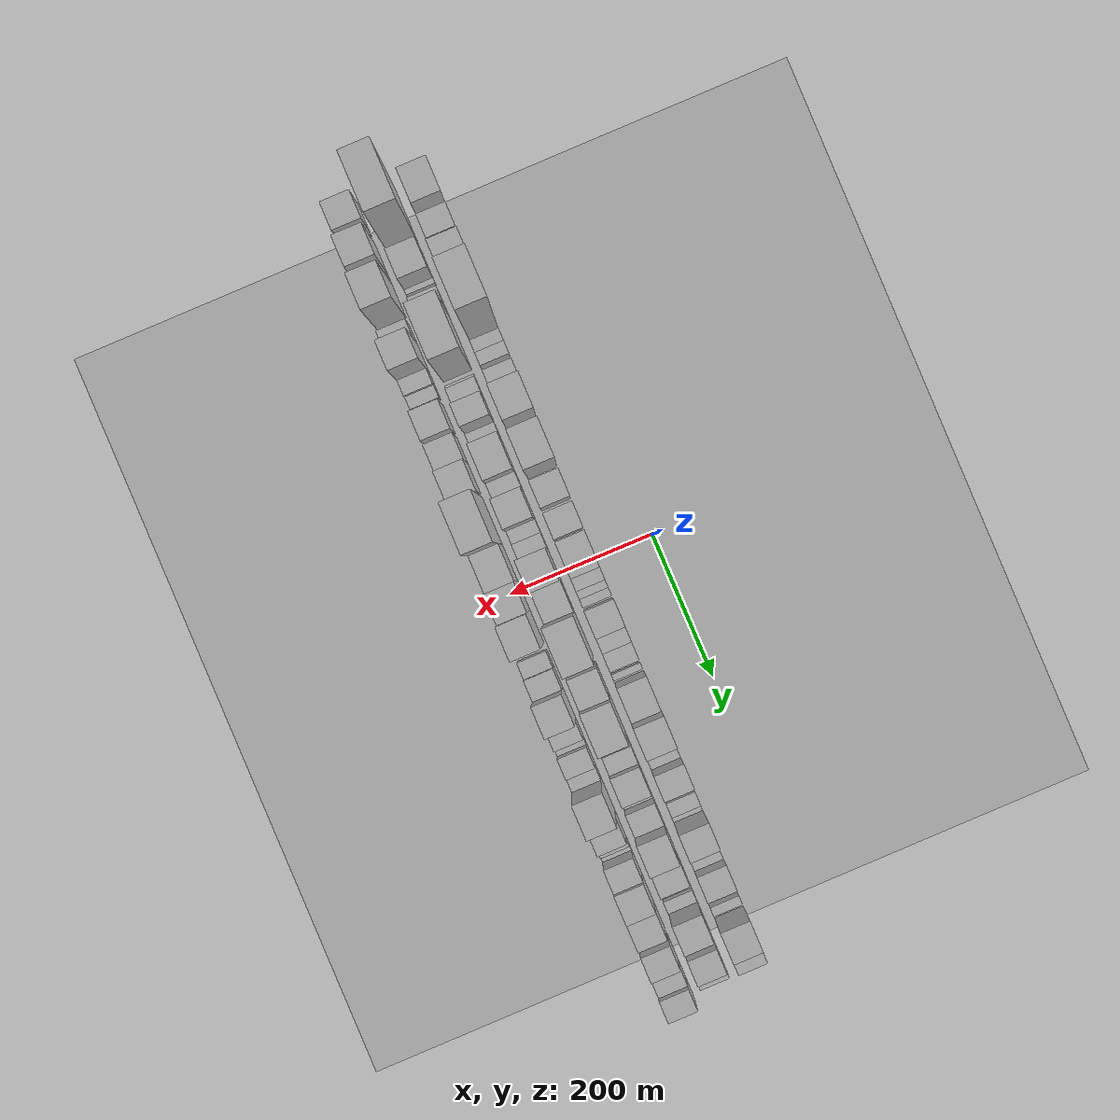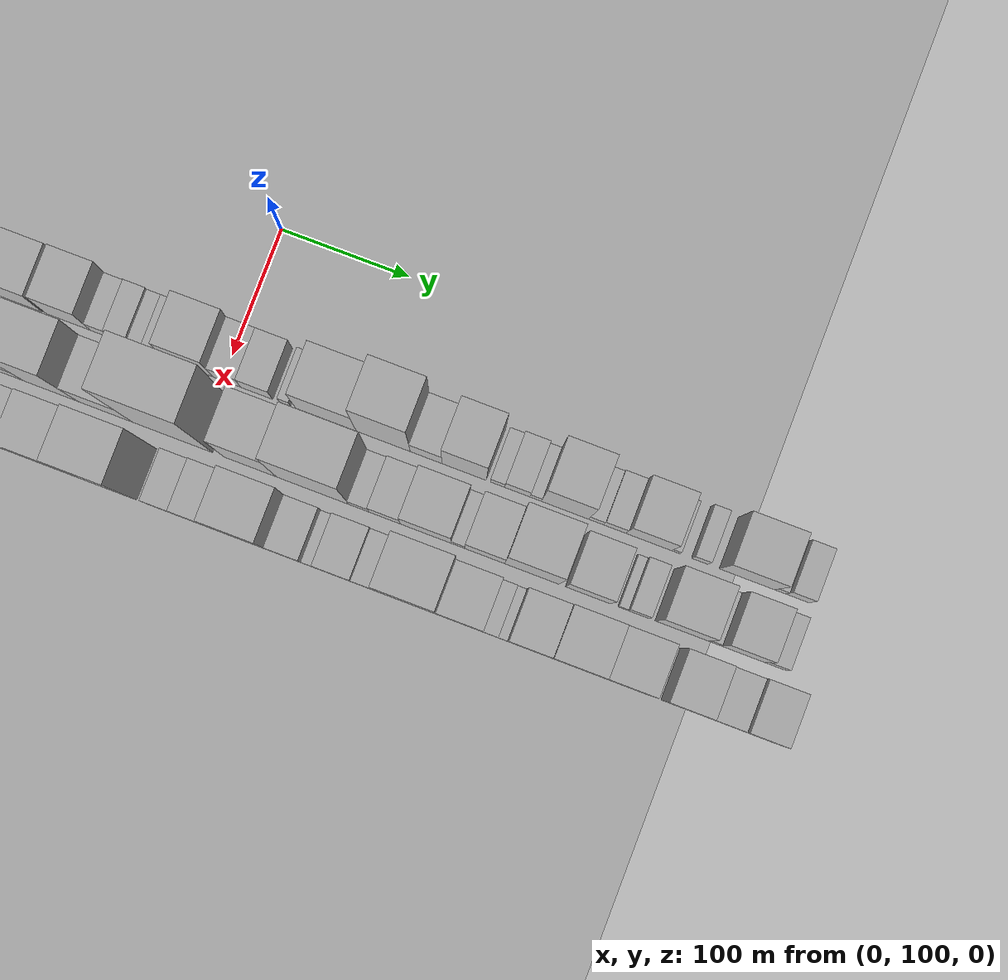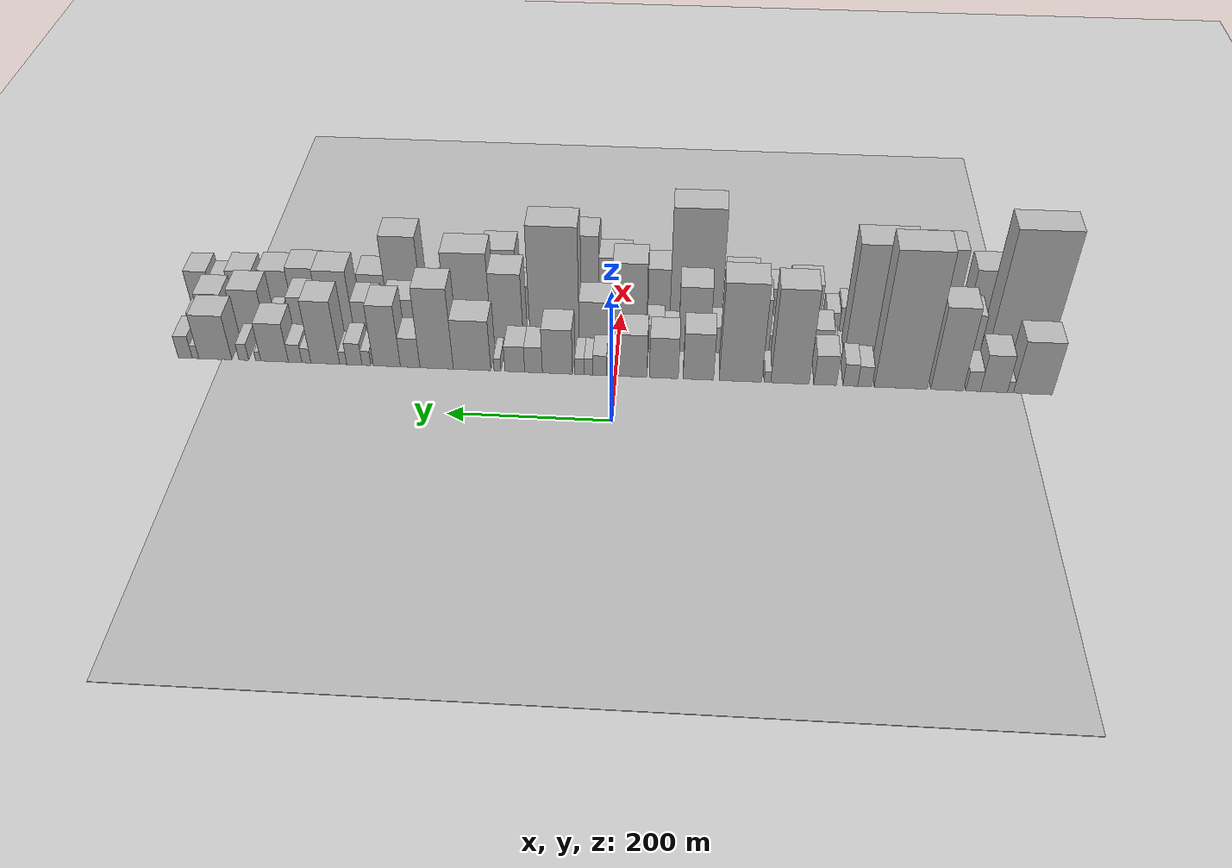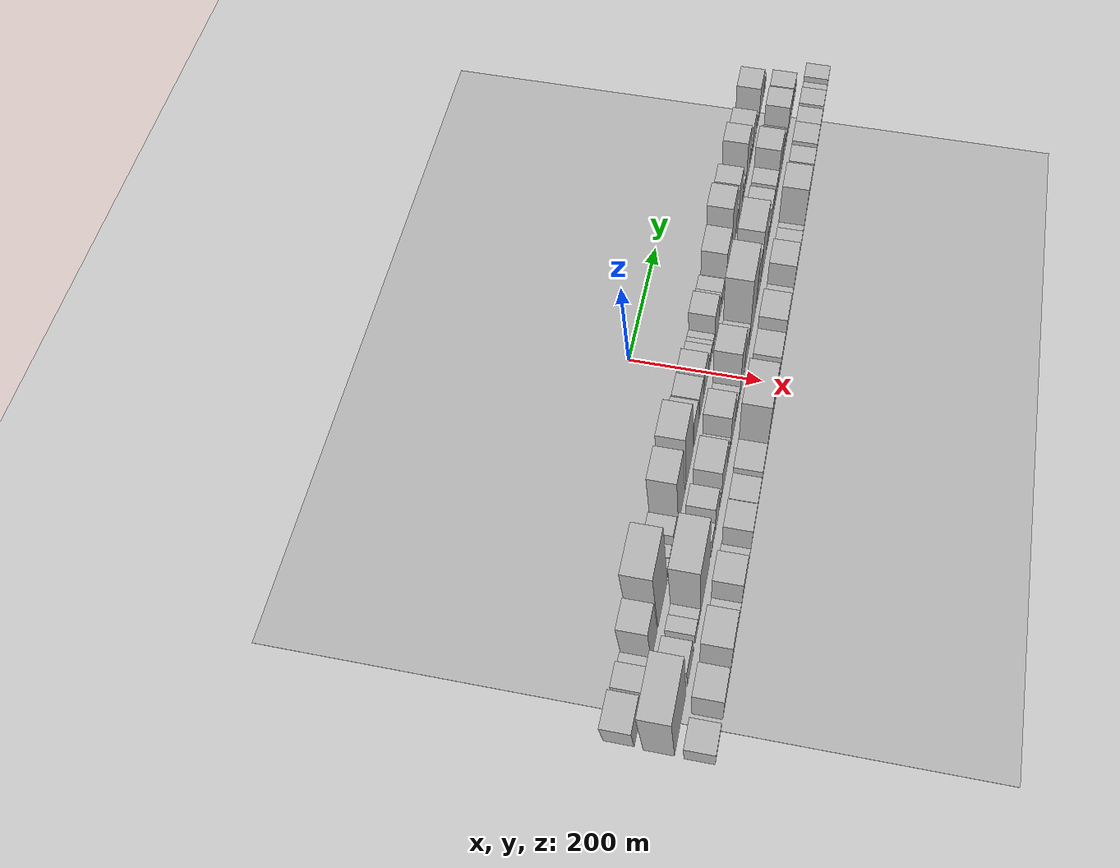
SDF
<?xml version="1.0" encoding="utf-8"?>

<sdf version="1.6">

   <world name="default">

      <gui fullscreen="0">

         <camera name="user_camera">

            <pose>-15 0 4.57585 0 0 0</pose>

            <view_controller>orbit</view_controller>

         </camera>

      </gui>

      <scene>

         <sky>

           <clouds>

             <speed>12</speed>

           </clouds>

         </sky>

         <ambient>0.4 0.4 0.4 1</ambient>

         <background>0.7 0.7 0.7 1</background>

         <shadows>1</shadows>

      </scene>

      <gravity>0 0 -9.8066</gravity>

      <magnetic_field>6e-06 2.3e-05 -4.2e-05</magnetic_field>

      <physics default="0" name="default_physics" type="ode">

         <ode>

            <solver>

               <type>quick</type>

               <iters>10</iters>

               <sor>1.0</sor>

               <use_dynamic_moi_rescaling>0</use_dynamic_moi_rescaling>

            </solver>

            <constraints>

               <cfm>0</cfm>

               <erp>0.2</erp>

               <contact_max_correcting_vel>100</contact_max_correcting_vel>

               <contact_surface_layer>0.001</contact_surface_layer>

            </constraints>

         </ode>

         <max_step_size>0.004</max_step_size>

         <real_time_factor>1</real_time_factor>

         <real_time_update_rate>250</real_time_update_rate>

      </physics>

      <light name="sun" type="directional">

         <cast_shadows>1</cast_shadows>

         <pose>0 0 10 0 0 0</pose>

         <diffuse>0.8 0.8 0.8 1</diffuse>

         <specular>0.2 0.2 0.2 1</specular>

         <attenuation>

            <range>1000</range>

            <constant>0.9</constant>

            <linear>0.01</linear>

            <quadratic>0.001</quadratic>

         </attenuation>

         <direction>-0.5 0.1 -0.9</direction>

      </light>

      <include>

         <name>ground_plane_1</name>

         <uri>model://HANNAS_ground_plane</uri>

         <pose>0 0 0  0 0 0</pose>

      </include>

      <include>

         <name>ground_plane_2</name>

         <uri>model://HANNAS_ground_plane</uri>

         <pose>100 0 0  0 0 0</pose>

      </include>

      <model name="building_1">

         <static>1</static>

         <pose frame="">100.0000 -514.2955 0 0.000000 0.000000 0.000000</pose>

         <link name="link">

            <pose frame="">0 0 42.00 0 0 0</pose>

            <collision name="collision">

               <geometry>

                  <box>

                     <size>40.0000 47.4091 84.0000</size>

                  </box>

               </geometry>

               <max_contacts>10</max_contacts>

               <surface>

                  <contact>

                     <ode/>

                  </contact>

                  <bounce/>

                  <friction>

                     <torsional>

                        <ode/>

                     </torsional>

                     <ode/>

                  </friction>

               </surface>

            </collision>

            <visual name="visual">

               <cast_shadows>0</cast_shadows>

               <geometry>

                  <box>

                     <size>40.0000 47.4091 84.0000</size>

                  </box>

               </geometry>

               <material>

                  <script>

                     <uri>model://HANNAS_wall/materials/scripts</uri>

                     <uri>model://HANNAS_wall/materials/textures</uri>

                     <name>vrc/HANNAS_wall</name>

                  </script>

               </material>

            </visual>

            <self_collide>0</self_collide>

            <enable_wind>0</enable_wind>

            <kinematic>0</kinematic>

         </link>

      </model>

      <model name="building_2">

         <static>1</static>

         <pose frame="">100.0000 -486.8983 0 0.000000 0.000000 0.000000</pose>

         <link name="link">

            <pose frame="">0 0 9.00 0 0 0</pose>

            <collision name="collision">

               <geometry>

                  <box>

                     <size>40.0000 7.3854 18.0000</size>

                  </box>

               </geometry>

               <max_contacts>10</max_contacts>

               <surface>

                  <contact>

                     <ode/>

                  </contact>

                  <bounce/>

                  <friction>

                     <torsional>

                        <ode/>

                     </torsional>

                     <ode/>

                  </friction>

               </surface>

            </collision>

            <visual name="visual">

               <cast_shadows>0</cast_shadows>

               <geometry>

                  <box>

                     <size>40.0000 7.3854 18.0000</size>

                  </box>

               </geometry>

               <material>

                  <script>

                     <uri>model://HANNAS_wall/materials/scripts</uri>

                     <uri>model://HANNAS_wall/materials/textures</uri>

                     <name>vrc/HANNAS_wall</name>

                  </script>

               </material>

            </visual>

            <self_collide>0</self_collide>

            <enable_wind>0</enable_wind>

            <kinematic>0</kinematic>

         </link>

      </model>

      <model name="building_3">

         <static>1</static>

         <pose frame="">100.0000 -466.7960 0 0.000000 0.000000 0.000000</pose>

         <link name="link">

            <pose frame="">0 0 30.00 0 0 0</pose>

            <collision name="collision">

               <geometry>

                  <box>

                     <size>40.0000 32.8191 60.0000</size>

                  </box>

               </geometry>

               <max_contacts>10</max_contacts>

               <surface>

                  <contact>

                     <ode/>

                  </contact>

                  <bounce/>

                  <friction>

                     <torsional>

                        <ode/>

                     </torsional>

                     <ode/>

                  </friction>

               </surface>

            </collision>

            <visual name="visual">

               <cast_shadows>0</cast_shadows>

               <geometry>

                  <box>

                     <size>40.0000 32.8191 60.0000</size>

                  </box>

               </geometry>

               <material>

                  <script>

                     <uri>model://HANNAS_wall/materials/scripts</uri>

                     <uri>model://HANNAS_wall/materials/textures</uri>

                     <name>vrc/HANNAS_wall</name>

                  </script>

               </material>

            </visual>

            <self_collide>0</self_collide>

            <enable_wind>0</enable_wind>

            <kinematic>0</kinematic>

         </link>

      </model>

      <model name="building_4">

         <static>1</static>

         <pose frame="">100.0000 -441.3647 0 0.000000 0.000000 0.000000</pose>

         <link name="link">

            <pose frame="">0 0 16.50 0 0 0</pose>

            <collision name="collision">

               <geometry>

                  <box>

                     <size>40.0000 18.0437 33.0000</size>

                  </box>

               </geometry>

               <max_contacts>10</max_contacts>

               <surface>

                  <contact>

                     <ode/>

                  </contact>

                  <bounce/>

                  <friction>

                     <torsional>

                        <ode/>

                     </torsional>

                     <ode/>

                  </friction>

               </surface>

            </collision>

            <visual name="visual">

               <cast_shadows>0</cast_shadows>

               <geometry>

                  <box>

                     <size>40.0000 18.0437 33.0000</size>

                  </box>

               </geometry>

               <material>

                  <script>

                     <uri>model://HANNAS_wall/materials/scripts</uri>

                     <uri>model://HANNAS_wall/materials/textures</uri>

                     <name>vrc/HANNAS_wall</name>

                  </script>

               </material>

            </visual>

            <self_collide>0</self_collide>

            <enable_wind>0</enable_wind>

            <kinematic>0</kinematic>

         </link>

      </model>

      <model name="building_5">

         <static>1</static>

         <pose frame="">100.0000 -409.4169 0 0.000000 0.000000 0.000000</pose>

         <link name="link">

            <pose frame="">0 0 66.00 0 0 0</pose>

            <collision name="collision">

               <geometry>

                  <box>

                     <size>40.0000 39.8519 132.0000</size>

                  </box>

               </geometry>

               <max_contacts>10</max_contacts>

               <surface>

                  <contact>

                     <ode/>

                  </contact>

                  <bounce/>

                  <friction>

                     <torsional>

                        <ode/>

                     </torsional>

                     <ode/>

                  </friction>

               </surface>

            </collision>

            <visual name="visual">

               <cast_shadows>0</cast_shadows>

               <geometry>

                  <box>

                     <size>40.0000 39.8519 132.0000</size>

                  </box>

               </geometry>

               <material>

                  <script>

                     <uri>model://HANNAS_wall/materials/scripts</uri>

                     <uri>model://HANNAS_wall/materials/textures</uri>

                     <name>vrc/HANNAS_wall</name>

                  </script>

               </material>

            </visual>

            <self_collide>0</self_collide>

            <enable_wind>0</enable_wind>

            <kinematic>0</kinematic>

         </link>

      </model>

      <model name="building_6">

         <static>1</static>

         <pose frame="">100.0000 -352.8863 0 0.000000 0.000000 0.000000</pose>

         <link name="link">

            <pose frame="">0 0 106.50 0 0 0</pose>

            <collision name="collision">

               <geometry>

                  <box>

                     <size>40.0000 65.2092 213.0000</size>

                  </box>

               </geometry>

               <max_contacts>10</max_contacts>

               <surface>

                  <contact>

                     <ode/>

                  </contact>

                  <bounce/>

                  <friction>

                     <torsional>

                        <ode/>

                     </torsional>

                     <ode/>

                  </friction>

               </surface>

            </collision>

            <visual name="visual">

               <cast_shadows>0</cast_shadows>

               <geometry>

                  <box>

                     <size>40.0000 65.2092 213.0000</size>

                  </box>

               </geometry>

               <material>

                  <script>

                     <uri>model://HANNAS_wall/materials/scripts</uri>

                     <uri>model://HANNAS_wall/materials/textures</uri>

                     <name>vrc/HANNAS_wall</name>

                  </script>

               </material>

            </visual>

            <self_collide>0</self_collide>

            <enable_wind>0</enable_wind>

            <kinematic>0</kinematic>

         </link>

      </model>

      <model name="building_7">

         <static>1</static>

         <pose frame="">100.0000 -308.5428 0 0.000000 0.000000 0.000000</pose>

         <link name="link">

            <pose frame="">0 0 16.50 0 0 0</pose>

            <collision name="collision">

               <geometry>

                  <box>

                     <size>40.0000 17.4778 33.0000</size>

                  </box>

               </geometry>

               <max_contacts>10</max_contacts>

               <surface>

                  <contact>

                     <ode/>

                  </contact>

                  <bounce/>

                  <friction>

                     <torsional>

                        <ode/>

                     </torsional>

                     <ode/>

                  </friction>

               </surface>

            </collision>

            <visual name="visual">

               <cast_shadows>0</cast_shadows>

               <geometry>

                  <box>

                     <size>40.0000 17.4778 33.0000</size>

                  </box>

               </geometry>

               <material>

                  <script>

                     <uri>model://HANNAS_wall/materials/scripts</uri>

                     <uri>model://HANNAS_wall/materials/textures</uri>

                     <name>vrc/HANNAS_wall</name>

                  </script>

               </material>

            </visual>

            <self_collide>0</self_collide>

            <enable_wind>0</enable_wind>

            <kinematic>0</kinematic>

         </link>

      </model>

      <model name="building_8">

         <static>1</static>

         <pose frame="">100.0000 -290.7510 0 0.000000 0.000000 0.000000</pose>

         <link name="link">

            <pose frame="">0 0 18.00 0 0 0</pose>

            <collision name="collision">

               <geometry>

                  <box>

                     <size>40.0000 18.1057 36.0000</size>

                  </box>

               </geometry>

               <max_contacts>10</max_contacts>

               <surface>

                  <contact>

                     <ode/>

                  </contact>

                  <bounce/>

                  <friction>

                     <torsional>

                        <ode/>

                     </torsional>

                     <ode/>

                  </friction>

               </surface>

            </collision>

            <visual name="visual">

               <cast_shadows>0</cast_shadows>

               <geometry>

                  <box>

                     <size>40.0000 18.1057 36.0000</size>

                  </box>

               </geometry>

               <material>

                  <script>

                     <uri>model://HANNAS_wall/materials/scripts</uri>

                     <uri>model://HANNAS_wall/materials/textures</uri>

                     <name>vrc/HANNAS_wall</name>

                  </script>

               </material>

            </visual>

            <self_collide>0</self_collide>

            <enable_wind>0</enable_wind>

            <kinematic>0</kinematic>

         </link>

      </model>

      <model name="building_9">

         <static>1</static>

         <pose frame="">100.0000 -259.7759 0 0.000000 0.000000 0.000000</pose>

         <link name="link">

            <pose frame="">0 0 24.00 0 0 0</pose>

            <collision name="collision">

               <geometry>

                  <box>

                     <size>40.0000 27.8445 48.0000</size>

                  </box>

               </geometry>

               <max_contacts>10</max_contacts>

               <surface>

                  <contact>

                     <ode/>

                  </contact>

                  <bounce/>

                  <friction>

                     <torsional>

                        <ode/>

                     </torsional>

                     <ode/>

                  </friction>

               </surface>

            </collision>

            <visual name="visual">

               <cast_shadows>0</cast_shadows>

               <geometry>

                  <box>

                     <size>40.0000 27.8445 48.0000</size>

                  </box>

               </geometry>

               <material>

                  <script>

                     <uri>model://HANNAS_wall/materials/scripts</uri>

                     <uri>model://HANNAS_wall/materials/textures</uri>

                     <name>vrc/HANNAS_wall</name>

                  </script>

               </material>

            </visual>

            <self_collide>0</self_collide>

            <enable_wind>0</enable_wind>

            <kinematic>0</kinematic>

         </link>

      </model>

      <model name="building_10">

         <static>1</static>

         <pose frame="">100.0000 -216.1852 0 0.000000 0.000000 0.000000</pose>

         <link name="link">

            <pose frame="">0 0 75.00 0 0 0</pose>

            <collision name="collision">

               <geometry>

                  <box>

                     <size>40.0000 47.3368 150.0000</size>

                  </box>

               </geometry>

               <max_contacts>10</max_contacts>

               <surface>

                  <contact>

                     <ode/>

                  </contact>

                  <bounce/>

                  <friction>

                     <torsional>

                        <ode/>

                     </torsional>

                     <ode/>

                  </friction>

               </surface>

            </collision>

            <visual name="visual">

               <cast_shadows>0</cast_shadows>

               <geometry>

                  <box>

                     <size>40.0000 47.3368 150.0000</size>

                  </box>

               </geometry>

               <material>

                  <script>

                     <uri>model://HANNAS_wall/materials/scripts</uri>

                     <uri>model://HANNAS_wall/materials/textures</uri>

                     <name>vrc/HANNAS_wall</name>

                  </script>

               </material>

            </visual>

            <self_collide>0</self_collide>

            <enable_wind>0</enable_wind>

            <kinematic>0</kinematic>

         </link>

      </model>

      <model name="building_11">

         <static>1</static>

         <pose frame="">100.0000 -188.3628 0 0.000000 0.000000 0.000000</pose>

         <link name="link">

            <pose frame="">0 0 9.00 0 0 0</pose>

            <collision name="collision">

               <geometry>

                  <box>

                     <size>40.0000 8.3081 18.0000</size>

                  </box>

               </geometry>

               <max_contacts>10</max_contacts>

               <surface>

                  <contact>

                     <ode/>

                  </contact>

                  <bounce/>

                  <friction>

                     <torsional>

                        <ode/>

                     </torsional>

                     <ode/>

                  </friction>

               </surface>

            </collision>

            <visual name="visual">

               <cast_shadows>0</cast_shadows>

               <geometry>

                  <box>

                     <size>40.0000 8.3081 18.0000</size>

                  </box>

               </geometry>

               <material>

                  <script>

                     <uri>model://HANNAS_wall/materials/scripts</uri>

                     <uri>model://HANNAS_wall/materials/textures</uri>

                     <name>vrc/HANNAS_wall</name>

                  </script>

               </material>

            </visual>

            <self_collide>0</self_collide>

            <enable_wind>0</enable_wind>

            <kinematic>0</kinematic>

         </link>

      </model>

      <model name="building_12">

         <static>1</static>

         <pose frame="">100.0000 -154.8625 0 0.000000 0.000000 0.000000</pose>

         <link name="link">

            <pose frame="">0 0 78.00 0 0 0</pose>

            <collision name="collision">

               <geometry>

                  <box>

                     <size>40.0000 52.6923 156.0000</size>

                  </box>

               </geometry>

               <max_contacts>10</max_contacts>

               <surface>

                  <contact>

                     <ode/>

                  </contact>

                  <bounce/>

                  <friction>

                     <torsional>

                        <ode/>

                     </torsional>

                     <ode/>

                  </friction>

               </surface>

            </collision>

            <visual name="visual">

               <cast_shadows>0</cast_shadows>

               <geometry>

                  <box>

                     <size>40.0000 52.6923 156.0000</size>

                  </box>

               </geometry>

               <material>

                  <script>

                     <uri>model://HANNAS_wall/materials/scripts</uri>

                     <uri>model://HANNAS_wall/materials/textures</uri>

                     <name>vrc/HANNAS_wall</name>

                  </script>

               </material>

            </visual>

            <self_collide>0</self_collide>

            <enable_wind>0</enable_wind>

            <kinematic>0</kinematic>

         </link>

      </model>

      <model name="building_13">

         <static>1</static>

         <pose frame="">100.0000 -102.5972 0 0.000000 0.000000 0.000000</pose>

         <link name="link">

            <pose frame="">0 0 37.50 0 0 0</pose>

            <collision name="collision">

               <geometry>

                  <box>

                     <size>40.0000 37.8382 75.0000</size>

                  </box>

               </geometry>

               <max_contacts>10</max_contacts>

               <surface>

                  <contact>

                     <ode/>

                  </contact>

                  <bounce/>

                  <friction>

                     <torsional>

                        <ode/>

                     </torsional>

                     <ode/>

                  </friction>

               </surface>

            </collision>

            <visual name="visual">

               <cast_shadows>0</cast_shadows>

               <geometry>

                  <box>

                     <size>40.0000 37.8382 75.0000</size>

                  </box>

               </geometry>

               <material>

                  <script>

                     <uri>model://HANNAS_wall/materials/scripts</uri>

                     <uri>model://HANNAS_wall/materials/textures</uri>

                     <name>vrc/HANNAS_wall</name>

                  </script>

               </material>

            </visual>

            <self_collide>0</self_collide>

            <enable_wind>0</enable_wind>

            <kinematic>0</kinematic>

         </link>

      </model>

      <model name="building_14">

         <static>1</static>

         <pose frame="">100.0000 -59.6214 0 0.000000 0.000000 0.000000</pose>

         <link name="link">

            <pose frame="">0 0 33.00 0 0 0</pose>

            <collision name="collision">

               <geometry>

                  <box>

                     <size>40.0000 36.1136 66.0000</size>

                  </box>

               </geometry>

               <max_contacts>10</max_contacts>

               <surface>

                  <contact>

                     <ode/>

                  </contact>

                  <bounce/>

                  <friction>

                     <torsional>

                        <ode/>

                     </torsional>

                     <ode/>

                  </friction>

               </surface>

            </collision>

            <visual name="visual">

               <cast_shadows>0</cast_shadows>

               <geometry>

                  <box>

                     <size>40.0000 36.1136 66.0000</size>

                  </box>

               </geometry>

               <material>

                  <script>

                     <uri>model://HANNAS_wall/materials/scripts</uri>

                     <uri>model://HANNAS_wall/materials/textures</uri>

                     <name>vrc/HANNAS_wall</name>

                  </script>

               </material>

            </visual>

            <self_collide>0</self_collide>

            <enable_wind>0</enable_wind>

            <kinematic>0</kinematic>

         </link>

      </model>

      <model name="building_15">

         <static>1</static>

         <pose frame="">100.0000 -21.0371 0 0.000000 0.000000 0.000000</pose>

         <link name="link">

            <pose frame="">0 0 34.50 0 0 0</pose>

            <collision name="collision">

               <geometry>

                  <box>

                     <size>40.0000 35.0550 69.0000</size>

                  </box>

               </geometry>

               <max_contacts>10</max_contacts>

               <surface>

                  <contact>

                     <ode/>

                  </contact>

                  <bounce/>

                  <friction>

                     <torsional>

                        <ode/>

                     </torsional>

                     <ode/>

                  </friction>

               </surface>

            </collision>

            <visual name="visual">

               <cast_shadows>0</cast_shadows>

               <geometry>

                  <box>

                     <size>40.0000 35.0550 69.0000</size>

                  </box>

               </geometry>

               <material>

                  <script>

                     <uri>model://HANNAS_wall/materials/scripts</uri>

                     <uri>model://HANNAS_wall/materials/textures</uri>

                     <name>vrc/HANNAS_wall</name>

                  </script>

               </material>

            </visual>

            <self_collide>0</self_collide>

            <enable_wind>0</enable_wind>

            <kinematic>0</kinematic>

         </link>

      </model>

      <model name="building_16">

         <static>1</static>

         <pose frame="">100.0000 4.1578 0 0.000000 0.000000 0.000000</pose>

         <link name="link">

            <pose frame="">0 0 15.00 0 0 0</pose>

            <collision name="collision">

               <geometry>

                  <box>

                     <size>40.0000 15.3347 30.0000</size>

                  </box>

               </geometry>

               <max_contacts>10</max_contacts>

               <surface>

                  <contact>

                     <ode/>

                  </contact>

                  <bounce/>

                  <friction>

                     <torsional>

                        <ode/>

                     </torsional>

                     <ode/>

                  </friction>

               </surface>

            </collision>

            <visual name="visual">

               <cast_shadows>0</cast_shadows>

               <geometry>

                  <box>

                     <size>40.0000 15.3347 30.0000</size>

                  </box>

               </geometry>

               <material>

                  <script>

                     <uri>model://HANNAS_wall/materials/scripts</uri>

                     <uri>model://HANNAS_wall/materials/textures</uri>

                     <name>vrc/HANNAS_wall</name>

                  </script>

               </material>

            </visual>

            <self_collide>0</self_collide>

            <enable_wind>0</enable_wind>

            <kinematic>0</kinematic>

         </link>

      </model>

      <model name="building_17">

         <static>1</static>

         <pose frame="">100.0000 20.5134 0 0.000000 0.000000 0.000000</pose>

         <link name="link">

            <pose frame="">0 0 16.50 0 0 0</pose>

            <collision name="collision">

               <geometry>

                  <box>

                     <size>40.0000 17.3766 33.0000</size>

                  </box>

               </geometry>

               <max_contacts>10</max_contacts>

               <surface>

                  <contact>

                     <ode/>

                  </contact>

                  <bounce/>

                  <friction>

                     <torsional>

                        <ode/>

                     </torsional>

                     <ode/>

                  </friction>

               </surface>

            </collision>

            <visual name="visual">

               <cast_shadows>0</cast_shadows>

               <geometry>

                  <box>

                     <size>40.0000 17.3766 33.0000</size>

                  </box>

               </geometry>

               <material>

                  <script>

                     <uri>model://HANNAS_wall/materials/scripts</uri>

                     <uri>model://HANNAS_wall/materials/textures</uri>

                     <name>vrc/HANNAS_wall</name>

                  </script>

               </material>

            </visual>

            <self_collide>0</self_collide>

            <enable_wind>0</enable_wind>

            <kinematic>0</kinematic>

         </link>

      </model>

      <model name="building_18">

         <static>1</static>

         <pose frame="">100.0000 34.6201 0 0.000000 0.000000 0.000000</pose>

         <link name="link">

            <pose frame="">0 0 13.50 0 0 0</pose>

            <collision name="collision">

               <geometry>

                  <box>

                     <size>40.0000 10.8368 27.0000</size>

                  </box>

               </geometry>

               <max_contacts>10</max_contacts>

               <surface>

                  <contact>

                     <ode/>

                  </contact>

                  <bounce/>

                  <friction>

                     <torsional>

                        <ode/>

                     </torsional>

                     <ode/>

                  </friction>

               </surface>

            </collision>

            <visual name="visual">

               <cast_shadows>0</cast_shadows>

               <geometry>

                  <box>

                     <size>40.0000 10.8368 27.0000</size>

                  </box>

               </geometry>

               <material>

                  <script>

                     <uri>model://HANNAS_wall/materials/scripts</uri>

                     <uri>model://HANNAS_wall/materials/textures</uri>

                     <name>vrc/HANNAS_wall</name>

                  </script>

               </material>

            </visual>

            <self_collide>0</self_collide>

            <enable_wind>0</enable_wind>

            <kinematic>0</kinematic>

         </link>

      </model>

      <model name="building_19">

         <static>1</static>

         <pose frame="">100.0000 45.8393 0 0.000000 0.000000 0.000000</pose>

         <link name="link">

            <pose frame="">0 0 13.50 0 0 0</pose>

            <collision name="collision">

               <geometry>

                  <box>

                     <size>40.0000 11.6015 27.0000</size>

                  </box>

               </geometry>

               <max_contacts>10</max_contacts>

               <surface>

                  <contact>

                     <ode/>

                  </contact>

                  <bounce/>

                  <friction>

                     <torsional>

                        <ode/>

                     </torsional>

                     <ode/>

                  </friction>

               </surface>

            </collision>

            <visual name="visual">

               <cast_shadows>0</cast_shadows>

               <geometry>

                  <box>

                     <size>40.0000 11.6015 27.0000</size>

                  </box>

               </geometry>

               <material>

                  <script>

                     <uri>model://HANNAS_wall/materials/scripts</uri>

                     <uri>model://HANNAS_wall/materials/textures</uri>

                     <name>vrc/HANNAS_wall</name>

                  </script>

               </material>

            </visual>

            <self_collide>0</self_collide>

            <enable_wind>0</enable_wind>

            <kinematic>0</kinematic>

         </link>

      </model>

      <model name="building_20">

         <static>1</static>

         <pose frame="">100.0000 73.5250 0 0.000000 0.000000 0.000000</pose>

         <link name="link">

            <pose frame="">0 0 36.00 0 0 0</pose>

            <collision name="collision">

               <geometry>

                  <box>

                     <size>40.0000 37.7700 72.0000</size>

                  </box>

               </geometry>

               <max_contacts>10</max_contacts>

               <surface>

                  <contact>

                     <ode/>

                  </contact>

                  <bounce/>

                  <friction>

                     <torsional>

                        <ode/>

                     </torsional>

                     <ode/>

                  </friction>

               </surface>

            </collision>

            <visual name="visual">

               <cast_shadows>0</cast_shadows>

               <geometry>

                  <box>

                     <size>40.0000 37.7700 72.0000</size>

                  </box>

               </geometry>

               <material>

                  <script>

                     <uri>model://HANNAS_wall/materials/scripts</uri>

                     <uri>model://HANNAS_wall/materials/textures</uri>

                     <name>vrc/HANNAS_wall</name>

                  </script>

               </material>

            </visual>

            <self_collide>0</self_collide>

            <enable_wind>0</enable_wind>

            <kinematic>0</kinematic>

         </link>

      </model>

      <model name="building_21">

         <static>1</static>

         <pose frame="">100.0000 103.5133 0 0.000000 0.000000 0.000000</pose>

         <link name="link">

            <pose frame="">0 0 21.00 0 0 0</pose>

            <collision name="collision">

               <geometry>

                  <box>

                     <size>40.0000 22.2065 42.0000</size>

                  </box>

               </geometry>

               <max_contacts>10</max_contacts>

               <surface>

                  <contact>

                     <ode/>

                  </contact>

                  <bounce/>

                  <friction>

                     <torsional>

                        <ode/>

                     </torsional>

                     <ode/>

                  </friction>

               </surface>

            </collision>

            <visual name="visual">

               <cast_shadows>0</cast_shadows>

               <geometry>

                  <box>

                     <size>40.0000 22.2065 42.0000</size>

                  </box>

               </geometry>

               <material>

                  <script>

                     <uri>model://HANNAS_wall/materials/scripts</uri>

                     <uri>model://HANNAS_wall/materials/textures</uri>

                     <name>vrc/HANNAS_wall</name>

                  </script>

               </material>

            </visual>

            <self_collide>0</self_collide>

            <enable_wind>0</enable_wind>

            <kinematic>0</kinematic>

         </link>

      </model>

      <model name="building_22">

         <static>1</static>

         <pose frame="">100.0000 127.0962 0 0.000000 0.000000 0.000000</pose>

         <link name="link">

            <pose frame="">0 0 21.00 0 0 0</pose>

            <collision name="collision">

               <geometry>

                  <box>

                     <size>40.0000 24.9593 42.0000</size>

                  </box>

               </geometry>

               <max_contacts>10</max_contacts>

               <surface>

                  <contact>

                     <ode/>

                  </contact>

                  <bounce/>

                  <friction>

                     <torsional>

                        <ode/>

                     </torsional>

                     <ode/>

                  </friction>

               </surface>

            </collision>

            <visual name="visual">

               <cast_shadows>0</cast_shadows>

               <geometry>

                  <box>

                     <size>40.0000 24.9593 42.0000</size>

                  </box>

               </geometry>

               <material>

                  <script>

                     <uri>model://HANNAS_wall/materials/scripts</uri>

                     <uri>model://HANNAS_wall/materials/textures</uri>

                     <name>vrc/HANNAS_wall</name>

                  </script>

               </material>

            </visual>

            <self_collide>0</self_collide>

            <enable_wind>0</enable_wind>

            <kinematic>0</kinematic>

         </link>

      </model>

      <model name="building_23">

         <static>1</static>

         <pose frame="">100.0000 148.9593 0 0.000000 0.000000 0.000000</pose>

         <link name="link">

            <pose frame="">0 0 10.50 0 0 0</pose>

            <collision name="collision">

               <geometry>

                  <box>

                     <size>40.0000 8.7669 21.0000</size>

                  </box>

               </geometry>

               <max_contacts>10</max_contacts>

               <surface>

                  <contact>

                     <ode/>

                  </contact>

                  <bounce/>

                  <friction>

                     <torsional>

                        <ode/>

                     </torsional>

                     <ode/>

                  </friction>

               </surface>

            </collision>

            <visual name="visual">

               <cast_shadows>0</cast_shadows>

               <geometry>

                  <box>

                     <size>40.0000 8.7669 21.0000</size>

                  </box>

               </geometry>

               <material>

                  <script>

                     <uri>model://HANNAS_wall/materials/scripts</uri>

                     <uri>model://HANNAS_wall/materials/textures</uri>

                     <name>vrc/HANNAS_wall</name>

                  </script>

               </material>

            </visual>

            <self_collide>0</self_collide>

            <enable_wind>0</enable_wind>

            <kinematic>0</kinematic>

         </link>

      </model>

      <model name="building_24">

         <static>1</static>

         <pose frame="">100.0000 181.0930 0 0.000000 0.000000 0.000000</pose>

         <link name="link">

            <pose frame="">0 0 40.50 0 0 0</pose>

            <collision name="collision">

               <geometry>

                  <box>

                     <size>40.0000 47.5004 81.0000</size>

                  </box>

               </geometry>

               <max_contacts>10</max_contacts>

               <surface>

                  <contact>

                     <ode/>

                  </contact>

                  <bounce/>

                  <friction>

                     <torsional>

                        <ode/>

                     </torsional>

                     <ode/>

                  </friction>

               </surface>

            </collision>

            <visual name="visual">

               <cast_shadows>0</cast_shadows>

               <geometry>

                  <box>

                     <size>40.0000 47.5004 81.0000</size>

                  </box>

               </geometry>

               <material>

                  <script>

                     <uri>model://HANNAS_wall/materials/scripts</uri>

                     <uri>model://HANNAS_wall/materials/textures</uri>

                     <name>vrc/HANNAS_wall</name>

                  </script>

               </material>

            </visual>

            <self_collide>0</self_collide>

            <enable_wind>0</enable_wind>

            <kinematic>0</kinematic>

         </link>

      </model>

      <model name="building_25">

         <static>1</static>

         <pose frame="">100.0000 225.9789 0 0.000000 0.000000 0.000000</pose>

         <link name="link">

            <pose frame="">0 0 64.50 0 0 0</pose>

            <collision name="collision">

               <geometry>

                  <box>

                     <size>40.0000 42.2713 129.0000</size>

                  </box>

               </geometry>

               <max_contacts>10</max_contacts>

               <surface>

                  <contact>

                     <ode/>

                  </contact>

                  <bounce/>

                  <friction>

                     <torsional>

                        <ode/>

                     </torsional>

                     <ode/>

                  </friction>

               </surface>

            </collision>

            <visual name="visual">

               <cast_shadows>0</cast_shadows>

               <geometry>

                  <box>

                     <size>40.0000 42.2713 129.0000</size>

                  </box>

               </geometry>

               <material>

                  <script>

                     <uri>model://HANNAS_wall/materials/scripts</uri>

                     <uri>model://HANNAS_wall/materials/textures</uri>

                     <name>vrc/HANNAS_wall</name>

                  </script>

               </material>

            </visual>

            <self_collide>0</self_collide>

            <enable_wind>0</enable_wind>

            <kinematic>0</kinematic>

         </link>

      </model>

      <model name="building_26">

         <static>1</static>

         <pose frame="">100.0000 259.4690 0 0.000000 0.000000 0.000000</pose>

         <link name="link">

            <pose frame="">0 0 24.00 0 0 0</pose>

            <collision name="collision">

               <geometry>

                  <box>

                     <size>40.0000 24.7089 48.0000</size>

                  </box>

               </geometry>

               <max_contacts>10</max_contacts>

               <surface>

                  <contact>

                     <ode/>

                  </contact>

                  <bounce/>

                  <friction>

                     <torsional>

                        <ode/>

                     </torsional>

                     <ode/>

                  </friction>

               </surface>

            </collision>

            <visual name="visual">

               <cast_shadows>0</cast_shadows>

               <geometry>

                  <box>

                     <size>40.0000 24.7089 48.0000</size>

                  </box>

               </geometry>

               <material>

                  <script>

                     <uri>model://HANNAS_wall/materials/scripts</uri>

                     <uri>model://HANNAS_wall/materials/textures</uri>

                     <name>vrc/HANNAS_wall</name>

                  </script>

               </material>

            </visual>

            <self_collide>0</self_collide>

            <enable_wind>0</enable_wind>

            <kinematic>0</kinematic>

         </link>

      </model>

      <model name="building_27">

         <static>1</static>

         <pose frame="">100.0000 289.0918 0 0.000000 0.000000 0.000000</pose>

         <link name="link">

            <pose frame="">0 0 49.50 0 0 0</pose>

            <collision name="collision">

               <geometry>

                  <box>

                     <size>40.0000 34.5367 99.0000</size>

                  </box>

               </geometry>

               <max_contacts>10</max_contacts>

               <surface>

                  <contact>

                     <ode/>

                  </contact>

                  <bounce/>

                  <friction>

                     <torsional>

                        <ode/>

                     </torsional>

                     <ode/>

                  </friction>

               </surface>

            </collision>

            <visual name="visual">

               <cast_shadows>0</cast_shadows>

               <geometry>

                  <box>

                     <size>40.0000 34.5367 99.0000</size>

                  </box>

               </geometry>

               <material>

                  <script>

                     <uri>model://HANNAS_wall/materials/scripts</uri>

                     <uri>model://HANNAS_wall/materials/textures</uri>

                     <name>vrc/HANNAS_wall</name>

                  </script>

               </material>

            </visual>

            <self_collide>0</self_collide>

            <enable_wind>0</enable_wind>

            <kinematic>0</kinematic>

         </link>

      </model>

      <model name="building_28">

         <static>1</static>

         <pose frame="">100.0000 315.0455 0 0.000000 0.000000 0.000000</pose>

         <link name="link">

            <pose frame="">0 0 12.00 0 0 0</pose>

            <collision name="collision">

               <geometry>

                  <box>

                     <size>40.0000 11.3708 24.0000</size>

                  </box>

               </geometry>

               <max_contacts>10</max_contacts>

               <surface>

                  <contact>

                     <ode/>

                  </contact>

                  <bounce/>

                  <friction>

                     <torsional>

                        <ode/>

                     </torsional>

                     <ode/>

                  </friction>

               </surface>

            </collision>

            <visual name="visual">

               <cast_shadows>0</cast_shadows>

               <geometry>

                  <box>

                     <size>40.0000 11.3708 24.0000</size>

                  </box>

               </geometry>

               <material>

                  <script>

                     <uri>model://HANNAS_wall/materials/scripts</uri>

                     <uri>model://HANNAS_wall/materials/textures</uri>

                     <name>vrc/HANNAS_wall</name>

                  </script>

               </material>

            </visual>

            <self_collide>0</self_collide>

            <enable_wind>0</enable_wind>

            <kinematic>0</kinematic>

         </link>

      </model>

      <model name="building_29">

         <static>1</static>

         <pose frame="">100.0000 330.5013 0 0.000000 0.000000 0.000000</pose>

         <link name="link">

            <pose frame="">0 0 18.00 0 0 0</pose>

            <collision name="collision">

               <geometry>

                  <box>

                     <size>40.0000 19.5408 36.0000</size>

                  </box>

               </geometry>

               <max_contacts>10</max_contacts>

               <surface>

                  <contact>

                     <ode/>

                  </contact>

                  <bounce/>

                  <friction>

                     <torsional>

                        <ode/>

                     </torsional>

                     <ode/>

                  </friction>

               </surface>

            </collision>

            <visual name="visual">

               <cast_shadows>0</cast_shadows>

               <geometry>

                  <box>

                     <size>40.0000 19.5408 36.0000</size>

                  </box>

               </geometry>

               <material>

                  <script>

                     <uri>model://HANNAS_wall/materials/scripts</uri>

                     <uri>model://HANNAS_wall/materials/textures</uri>

                     <name>vrc/HANNAS_wall</name>

                  </script>

               </material>

            </visual>

            <self_collide>0</self_collide>

            <enable_wind>0</enable_wind>

            <kinematic>0</kinematic>

         </link>

      </model>

      <model name="building_30">

         <static>1</static>

         <pose frame="">100.0000 344.7738 0 0.000000 0.000000 0.000000</pose>

         <link name="link">

            <pose frame="">0 0 10.50 0 0 0</pose>

            <collision name="collision">

               <geometry>

                  <box>

                     <size>40.0000 9.0042 21.0000</size>

                  </box>

               </geometry>

               <max_contacts>10</max_contacts>

               <surface>

                  <contact>

                     <ode/>

                  </contact>

                  <bounce/>

                  <friction>

                     <torsional>

                        <ode/>

                     </torsional>

                     <ode/>

                  </friction>

               </surface>

            </collision>

            <visual name="visual">

               <cast_shadows>0</cast_shadows>

               <geometry>

                  <box>

                     <size>40.0000 9.0042 21.0000</size>

                  </box>

               </geometry>

               <material>

                  <script>

                     <uri>model://HANNAS_wall/materials/scripts</uri>

                     <uri>model://HANNAS_wall/materials/textures</uri>

                     <name>vrc/HANNAS_wall</name>

                  </script>

               </material>

            </visual>

            <self_collide>0</self_collide>

            <enable_wind>0</enable_wind>

            <kinematic>0</kinematic>

         </link>

      </model>

      <model name="building_31">

         <static>1</static>

         <pose frame="">100.0000 367.6238 0 0.000000 0.000000 0.000000</pose>

         <link name="link">

            <pose frame="">0 0 51.00 0 0 0</pose>

            <collision name="collision">

               <geometry>

                  <box>

                     <size>40.0000 36.6956 102.0000</size>

                  </box>

               </geometry>

               <max_contacts>10</max_contacts>

               <surface>

                  <contact>

                     <ode/>

                  </contact>

                  <bounce/>

                  <friction>

                     <torsional>

                        <ode/>

                     </torsional>

                     <ode/>

                  </friction>

               </surface>

            </collision>

            <visual name="visual">

               <cast_shadows>0</cast_shadows>

               <geometry>

                  <box>

                     <size>40.0000 36.6956 102.0000</size>

                  </box>

               </geometry>

               <material>

                  <script>

                     <uri>model://HANNAS_wall/materials/scripts</uri>

                     <uri>model://HANNAS_wall/materials/textures</uri>

                     <name>vrc/HANNAS_wall</name>

                  </script>

               </material>

            </visual>

            <self_collide>0</self_collide>

            <enable_wind>0</enable_wind>

            <kinematic>0</kinematic>

         </link>

      </model>

      <model name="building_32">

         <static>1</static>

         <pose frame="">100.0000 391.7401 0 0.000000 0.000000 0.000000</pose>

         <link name="link">

            <pose frame="">0 0 12.00 0 0 0</pose>

            <collision name="collision">

               <geometry>

                  <box>

                     <size>40.0000 11.5371 24.0000</size>

                  </box>

               </geometry>

               <max_contacts>10</max_contacts>

               <surface>

                  <contact>

                     <ode/>

                  </contact>

                  <bounce/>

                  <friction>

                     <torsional>

                        <ode/>

                     </torsional>

                     <ode/>

                  </friction>

               </surface>

            </collision>

            <visual name="visual">

               <cast_shadows>0</cast_shadows>

               <geometry>

                  <box>

                     <size>40.0000 11.5371 24.0000</size>

                  </box>

               </geometry>

               <material>

                  <script>

                     <uri>model://HANNAS_wall/materials/scripts</uri>

                     <uri>model://HANNAS_wall/materials/textures</uri>

                     <name>vrc/HANNAS_wall</name>

                  </script>

               </material>

            </visual>

            <self_collide>0</self_collide>

            <enable_wind>0</enable_wind>

            <kinematic>0</kinematic>

         </link>

      </model>

      <model name="building_33">

         <static>1</static>

         <pose frame="">100.0000 406.1605 0 0.000000 0.000000 0.000000</pose>

         <link name="link">

            <pose frame="">0 0 15.00 0 0 0</pose>

            <collision name="collision">

               <geometry>

                  <box>

                     <size>40.0000 17.3037 30.0000</size>

                  </box>

               </geometry>

               <max_contacts>10</max_contacts>

               <surface>

                  <contact>

                     <ode/>

                  </contact>

                  <bounce/>

                  <friction>

                     <torsional>

                        <ode/>

                     </torsional>

                     <ode/>

                  </friction>

               </surface>

            </collision>

            <visual name="visual">

               <cast_shadows>0</cast_shadows>

               <geometry>

                  <box>

                     <size>40.0000 17.3037 30.0000</size>

                  </box>

               </geometry>

               <material>

                  <script>

                     <uri>model://HANNAS_wall/materials/scripts</uri>

                     <uri>model://HANNAS_wall/materials/textures</uri>

                     <name>vrc/HANNAS_wall</name>

                  </script>

               </material>

            </visual>

            <self_collide>0</self_collide>

            <enable_wind>0</enable_wind>

            <kinematic>0</kinematic>

         </link>

      </model>

      <model name="building_34">

         <static>1</static>

         <pose frame="">100.0000 432.5061 0 0.000000 0.000000 0.000000</pose>

         <link name="link">

            <pose frame="">0 0 31.50 0 0 0</pose>

            <collision name="collision">

               <geometry>

                  <box>

                     <size>40.0000 35.3875 63.0000</size>

                  </box>

               </geometry>

               <max_contacts>10</max_contacts>

               <surface>

                  <contact>

                     <ode/>

                  </contact>

                  <bounce/>

                  <friction>

                     <torsional>

                        <ode/>

                     </torsional>

                     <ode/>

                  </friction>

               </surface>

            </collision>

            <visual name="visual">

               <cast_shadows>0</cast_shadows>

               <geometry>

                  <box>

                     <size>40.0000 35.3875 63.0000</size>

                  </box>

               </geometry>

               <material>

                  <script>

                     <uri>model://HANNAS_wall/materials/scripts</uri>

                     <uri>model://HANNAS_wall/materials/textures</uri>

                     <name>vrc/HANNAS_wall</name>

                  </script>

               </material>

            </visual>

            <self_collide>0</self_collide>

            <enable_wind>0</enable_wind>

            <kinematic>0</kinematic>

         </link>

      </model>

      <model name="building_35">

         <static>1</static>

         <pose frame="">100.0000 453.4936 0 0.000000 0.000000 0.000000</pose>

         <link name="link">

            <pose frame="">0 0 7.50 0 0 0</pose>

            <collision name="collision">

               <geometry>

                  <box>

                     <size>40.0000 6.5874 15.0000</size>

                  </box>

               </geometry>

               <max_contacts>10</max_contacts>

               <surface>

                  <contact>

                     <ode/>

                  </contact>

                  <bounce/>

                  <friction>

                     <torsional>

                        <ode/>

                     </torsional>

                     <ode/>

                  </friction>

               </surface>

            </collision>

            <visual name="visual">

               <cast_shadows>0</cast_shadows>

               <geometry>

                  <box>

                     <size>40.0000 6.5874 15.0000</size>

                  </box>

               </geometry>

               <material>

                  <script>

                     <uri>model://HANNAS_wall/materials/scripts</uri>

                     <uri>model://HANNAS_wall/materials/textures</uri>

                     <name>vrc/HANNAS_wall</name>

                  </script>

               </material>

            </visual>

            <self_collide>0</self_collide>

            <enable_wind>0</enable_wind>

            <kinematic>0</kinematic>

         </link>

      </model>

      <model name="building_36">

         <static>1</static>

         <pose frame="">100.0000 472.0813 0 0.000000 0.000000 0.000000</pose>

         <link name="link">

            <pose frame="">0 0 13.50 0 0 0</pose>

            <collision name="collision">

               <geometry>

                  <box>

                     <size>40.0000 12.5881 27.0000</size>

                  </box>

               </geometry>

               <max_contacts>10</max_contacts>

               <surface>

                  <contact>

                     <ode/>

                  </contact>

                  <bounce/>

                  <friction>

                     <torsional>

                        <ode/>

                     </torsional>

                     <ode/>

                  </friction>

               </surface>

            </collision>

            <visual name="visual">

               <cast_shadows>0</cast_shadows>

               <geometry>

                  <box>

                     <size>40.0000 12.5881 27.0000</size>

                  </box>

               </geometry>

               <material>

                  <script>

                     <uri>model://HANNAS_wall/materials/scripts</uri>

                     <uri>model://HANNAS_wall/materials/textures</uri>

                     <name>vrc/HANNAS_wall</name>

                  </script>

               </material>

            </visual>

            <self_collide>0</self_collide>

            <enable_wind>0</enable_wind>

            <kinematic>0</kinematic>

         </link>

      </model>

      <model name="building_37">

         <static>1</static>

         <pose frame="">100.0000 508.7297 0 0.000000 0.000000 0.000000</pose>

         <link name="link">

            <pose frame="">0 0 36.00 0 0 0</pose>

            <collision name="collision">

               <geometry>

                  <box>

                     <size>40.0000 42.7086 72.0000</size>

                  </box>

               </geometry>

               <max_contacts>10</max_contacts>

               <surface>

                  <contact>

                     <ode/>

                  </contact>

                  <bounce/>

                  <friction>

                     <torsional>

                        <ode/>

                     </torsional>

                     <ode/>

                  </friction>

               </surface>

            </collision>

            <visual name="visual">

               <cast_shadows>0</cast_shadows>

               <geometry>

                  <box>

                     <size>40.0000 42.7086 72.0000</size>

                  </box>

               </geometry>

               <material>

                  <script>

                     <uri>model://HANNAS_wall/materials/scripts</uri>

                     <uri>model://HANNAS_wall/materials/textures</uri>

                     <name>vrc/HANNAS_wall</name>

                  </script>

               </material>

            </visual>

            <self_collide>0</self_collide>

            <enable_wind>0</enable_wind>

            <kinematic>0</kinematic>

         </link>

      </model>

      <model name="building_38">

         <static>1</static>

         <pose frame="">100.0000 534.2845 0 0.000000 0.000000 0.000000</pose>

         <link name="link">

            <pose frame="">0 0 10.50 0 0 0</pose>

            <collision name="collision">

               <geometry>

                  <box>

                     <size>40.0000 8.4009 21.0000</size>

                  </box>

               </geometry>

               <max_contacts>10</max_contacts>

               <surface>

                  <contact>

                     <ode/>

                  </contact>

                  <bounce/>

                  <friction>

                     <torsional>

                        <ode/>

                     </torsional>

                     <ode/>

                  </friction>

               </surface>

            </collision>

            <visual name="visual">

               <cast_shadows>0</cast_shadows>

               <geometry>

                  <box>

                     <size>40.0000 8.4009 21.0000</size>

                  </box>

               </geometry>

               <material>

                  <script>

                     <uri>model://HANNAS_wall/materials/scripts</uri>

                     <uri>model://HANNAS_wall/materials/textures</uri>

                     <name>vrc/HANNAS_wall</name>

                  </script>

               </material>

            </visual>

            <self_collide>0</self_collide>

            <enable_wind>0</enable_wind>

            <kinematic>0</kinematic>

         </link>

      </model>

      <model name="building_39">

         <static>1</static>

         <pose frame="">100.0000 547.5120 0 0.000000 0.000000 0.000000</pose>

         <link name="link">

            <pose frame="">0 0 18.00 0 0 0</pose>

            <collision name="collision">

               <geometry>

                  <box>

                     <size>40.0000 18.0543 36.0000</size>

                  </box>

               </geometry>

               <max_contacts>10</max_contacts>

               <surface>

                  <contact>

                     <ode/>

                  </contact>

                  <bounce/>

                  <friction>

                     <torsional>

                        <ode/>

                     </torsional>

                     <ode/>

                  </friction>

               </surface>

            </collision>

            <visual name="visual">

               <cast_shadows>0</cast_shadows>

               <geometry>

                  <box>

                     <size>40.0000 18.0543 36.0000</size>

                  </box>

               </geometry>

               <material>

                  <script>

                     <uri>model://HANNAS_wall/materials/scripts</uri>

                     <uri>model://HANNAS_wall/materials/textures</uri>

                     <name>vrc/HANNAS_wall</name>

                  </script>

               </material>

            </visual>

            <self_collide>0</self_collide>

            <enable_wind>0</enable_wind>

            <kinematic>0</kinematic>

         </link>

      </model>

      <model name="building_40">

         <static>1</static>

         <pose frame="">152.0000 -501.7567 0 0.000000 0.000000 0.000000</pose>

         <link name="link">

            <pose frame="">0 0 105.00 0 0 0</pose>

            <collision name="collision">

               <geometry>

                  <box>

                     <size>40.0000 76.4865 210.0000</size>

                  </box>

               </geometry>

               <max_contacts>10</max_contacts>

               <surface>

                  <contact>

                     <ode/>

                  </contact>

                  <bounce/>

                  <friction>

                     <torsional>

                        <ode/>

                     </torsional>

                     <ode/>

                  </friction>

               </surface>

            </collision>

            <visual name="visual">

               <cast_shadows>0</cast_shadows>

               <geometry>

                  <box>

                     <size>40.0000 76.4865 210.0000</size>

                  </box>

               </geometry>

               <material>

                  <script>

                     <uri>model://HANNAS_wall/materials/scripts</uri>

                     <uri>model://HANNAS_wall/materials/textures</uri>

                     <name>vrc/HANNAS_wall</name>

                  </script>

               </material>

            </visual>

            <self_collide>0</self_collide>

            <enable_wind>0</enable_wind>

            <kinematic>0</kinematic>

         </link>

      </model>

      <model name="building_41">

         <static>1</static>

         <pose frame="">152.0000 -433.1992 0 0.000000 0.000000 0.000000</pose>

         <link name="link">

            <pose frame="">0 0 39.00 0 0 0</pose>

            <collision name="collision">

               <geometry>

                  <box>

                     <size>40.0000 40.6286 78.0000</size>

                  </box>

               </geometry>

               <max_contacts>10</max_contacts>

               <surface>

                  <contact>

                     <ode/>

                  </contact>

                  <bounce/>

                  <friction>

                     <torsional>

                        <ode/>

                     </torsional>

                     <ode/>

                  </friction>

               </surface>

            </collision>

            <visual name="visual">

               <cast_shadows>0</cast_shadows>

               <geometry>

                  <box>

                     <size>40.0000 40.6286 78.0000</size>

                  </box>

               </geometry>

               <material>

                  <script>

                     <uri>model://HANNAS_wall/materials/scripts</uri>

                     <uri>model://HANNAS_wall/materials/textures</uri>

                     <name>vrc/HANNAS_wall</name>

                  </script>

               </material>

            </visual>

            <self_collide>0</self_collide>

            <enable_wind>0</enable_wind>

            <kinematic>0</kinematic>

         </link>

      </model>

      <model name="building_42">

         <static>1</static>

         <pose frame="">152.0000 -409.1703 0 0.000000 0.000000 0.000000</pose>

         <link name="link">

            <pose frame="">0 0 7.50 0 0 0</pose>

            <collision name="collision">

               <geometry>

                  <box>

                     <size>40.0000 7.4292 15.0000</size>

                  </box>

               </geometry>

               <max_contacts>10</max_contacts>

               <surface>

                  <contact>

                     <ode/>

                  </contact>

                  <bounce/>

                  <friction>

                     <torsional>

                        <ode/>

                     </torsional>

                     <ode/>

                  </friction>

               </surface>

            </collision>

            <visual name="visual">

               <cast_shadows>0</cast_shadows>

               <geometry>

                  <box>

                     <size>40.0000 7.4292 15.0000</size>

                  </box>

               </geometry>

               <material>

                  <script>

                     <uri>model://HANNAS_wall/materials/scripts</uri>

                     <uri>model://HANNAS_wall/materials/textures</uri>

                     <name>vrc/HANNAS_wall</name>

                  </script>

               </material>

            </visual>

            <self_collide>0</self_collide>

            <enable_wind>0</enable_wind>

            <kinematic>0</kinematic>

         </link>

      </model>

      <model name="building_43">

         <static>1</static>

         <pose frame="">152.0000 -385.8464 0 0.000000 0.000000 0.000000</pose>

         <link name="link">

            <pose frame="">0 0 19.50 0 0 0</pose>

            <collision name="collision">

               <geometry>

                  <box>

                     <size>40.0000 21.2186 39.0000</size>

                  </box>

               </geometry>

               <max_contacts>10</max_contacts>

               <surface>

                  <contact>

                     <ode/>

                  </contact>

                  <bounce/>

                  <friction>

                     <torsional>

                        <ode/>

                     </torsional>

                     <ode/>

                  </friction>

               </surface>

            </collision>

            <visual name="visual">

               <cast_shadows>0</cast_shadows>

               <geometry>

                  <box>

                     <size>40.0000 21.2186 39.0000</size>

                  </box>

               </geometry>

               <material>

                  <script>

                     <uri>model://HANNAS_wall/materials/scripts</uri>

                     <uri>model://HANNAS_wall/materials/textures</uri>

                     <name>vrc/HANNAS_wall</name>

                  </script>

               </material>

            </visual>

            <self_collide>0</self_collide>

            <enable_wind>0</enable_wind>

            <kinematic>0</kinematic>

         </link>

      </model>

      <model name="building_44">

         <static>1</static>

         <pose frame="">152.0000 -366.7933 0 0.000000 0.000000 0.000000</pose>

         <link name="link">

            <pose frame="">0 0 15.00 0 0 0</pose>

            <collision name="collision">

               <geometry>

                  <box>

                     <size>40.0000 16.8875 30.0000</size>

                  </box>

               </geometry>

               <max_contacts>10</max_contacts>

               <surface>

                  <contact>

                     <ode/>

                  </contact>

                  <bounce/>

                  <friction>

                     <torsional>

                        <ode/>

                     </torsional>

                     <ode/>

                  </friction>

               </surface>

            </collision>

            <visual name="visual">

               <cast_shadows>0</cast_shadows>

               <geometry>

                  <box>

                     <size>40.0000 16.8875 30.0000</size>

                  </box>

               </geometry>

               <material>

                  <script>

                     <uri>model://HANNAS_wall/materials/scripts</uri>

                     <uri>model://HANNAS_wall/materials/textures</uri>

                     <name>vrc/HANNAS_wall</name>

                  </script>

               </material>

            </visual>

            <self_collide>0</self_collide>

            <enable_wind>0</enable_wind>

            <kinematic>0</kinematic>

         </link>

      </model>

      <model name="building_45">

         <static>1</static>

         <pose frame="">152.0000 -322.4286 0 0.000000 0.000000 0.000000</pose>

         <link name="link">

            <pose frame="">0 0 90.00 0 0 0</pose>

            <collision name="collision">

               <geometry>

                  <box>

                     <size>40.0000 71.8419 180.0000</size>

                  </box>

               </geometry>

               <max_contacts>10</max_contacts>

               <surface>

                  <contact>

                     <ode/>

                  </contact>

                  <bounce/>

                  <friction>

                     <torsional>

                        <ode/>

                     </torsional>

                     <ode/>

                  </friction>

               </surface>

            </collision>

            <visual name="visual">

               <cast_shadows>0</cast_shadows>

               <geometry>

                  <box>

                     <size>40.0000 71.8419 180.0000</size>

                  </box>

               </geometry>

               <material>

                  <script>

                     <uri>model://HANNAS_wall/materials/scripts</uri>

                     <uri>model://HANNAS_wall/materials/textures</uri>

                     <name>vrc/HANNAS_wall</name>

                  </script>

               </material>

            </visual>

            <self_collide>0</self_collide>

            <enable_wind>0</enable_wind>

            <kinematic>0</kinematic>

         </link>

      </model>

      <model name="building_46">

         <static>1</static>

         <pose frame="">152.0000 -274.7746 0 0.000000 0.000000 0.000000</pose>

         <link name="link">

            <pose frame="">0 0 9.00 0 0 0</pose>

            <collision name="collision">

               <geometry>

                  <box>

                     <size>40.0000 7.4662 18.0000</size>

                  </box>

               </geometry>

               <max_contacts>10</max_contacts>

               <surface>

                  <contact>

                     <ode/>

                  </contact>

                  <bounce/>

                  <friction>

                     <torsional>

                        <ode/>

                     </torsional>

                     <ode/>

                  </friction>

               </surface>

            </collision>

            <visual name="visual">

               <cast_shadows>0</cast_shadows>

               <geometry>

                  <box>

                     <size>40.0000 7.4662 18.0000</size>

                  </box>

               </geometry>

               <material>

                  <script>

                     <uri>model://HANNAS_wall/materials/scripts</uri>

                     <uri>model://HANNAS_wall/materials/textures</uri>

                     <name>vrc/HANNAS_wall</name>

                  </script>

               </material>

            </visual>

            <self_collide>0</self_collide>

            <enable_wind>0</enable_wind>

            <kinematic>0</kinematic>

         </link>

      </model>

      <model name="building_47">

         <static>1</static>

         <pose frame="">152.0000 -257.5710 0 0.000000 0.000000 0.000000</pose>

         <link name="link">

            <pose frame="">0 0 22.50 0 0 0</pose>

            <collision name="collision">

               <geometry>

                  <box>

                     <size>40.0000 26.9411 45.0000</size>

                  </box>

               </geometry>

               <max_contacts>10</max_contacts>

               <surface>

                  <contact>

                     <ode/>

                  </contact>

                  <bounce/>

                  <friction>

                     <torsional>

                        <ode/>

                     </torsional>

                     <ode/>

                  </friction>

               </surface>

            </collision>

            <visual name="visual">

               <cast_shadows>0</cast_shadows>

               <geometry>

                  <box>

                     <size>40.0000 26.9411 45.0000</size>

                  </box>

               </geometry>

               <material>

                  <script>

                     <uri>model://HANNAS_wall/materials/scripts</uri>

                     <uri>model://HANNAS_wall/materials/textures</uri>

                     <name>vrc/HANNAS_wall</name>

                  </script>

               </material>

            </visual>

            <self_collide>0</self_collide>

            <enable_wind>0</enable_wind>

            <kinematic>0</kinematic>

         </link>

      </model>

      <model name="building_48">

         <static>1</static>

         <pose frame="">152.0000 -228.5603 0 0.000000 0.000000 0.000000</pose>

         <link name="link">

            <pose frame="">0 0 46.50 0 0 0</pose>

            <collision name="collision">

               <geometry>

                  <box>

                     <size>40.0000 31.0802 93.0000</size>

                  </box>

               </geometry>

               <max_contacts>10</max_contacts>

               <surface>

                  <contact>

                     <ode/>

                  </contact>

                  <bounce/>

                  <friction>

                     <torsional>

                        <ode/>

                     </torsional>

                     <ode/>

                  </friction>

               </surface>

            </collision>

            <visual name="visual">

               <cast_shadows>0</cast_shadows>

               <geometry>

                  <box>

                     <size>40.0000 31.0802 93.0000</size>

                  </box>

               </geometry>

               <material>

                  <script>

                     <uri>model://HANNAS_wall/materials/scripts</uri>

                     <uri>model://HANNAS_wall/materials/textures</uri>

                     <name>vrc/HANNAS_wall</name>

                  </script>

               </material>

            </visual>

            <self_collide>0</self_collide>

            <enable_wind>0</enable_wind>

            <kinematic>0</kinematic>

         </link>

      </model>

      <model name="building_49">

         <static>1</static>

         <pose frame="">152.0000 -200.5107 0 0.000000 0.000000 0.000000</pose>

         <link name="link">

            <pose frame="">0 0 16.50 0 0 0</pose>

            <collision name="collision">

               <geometry>

                  <box>

                     <size>40.0000 19.0191 33.0000</size>

                  </box>

               </geometry>

               <max_contacts>10</max_contacts>

               <surface>

                  <contact>

                     <ode/>

                  </contact>

                  <bounce/>

                  <friction>

                     <torsional>

                        <ode/>

                     </torsional>

                     <ode/>

                  </friction>

               </surface>

            </collision>

            <visual name="visual">

               <cast_shadows>0</cast_shadows>

               <geometry>

                  <box>

                     <size>40.0000 19.0191 33.0000</size>

                  </box>

               </geometry>

               <material>

                  <script>

                     <uri>model://HANNAS_wall/materials/scripts</uri>

                     <uri>model://HANNAS_wall/materials/textures</uri>

                     <name>vrc/HANNAS_wall</name>

                  </script>

               </material>

            </visual>

            <self_collide>0</self_collide>

            <enable_wind>0</enable_wind>

            <kinematic>0</kinematic>

         </link>

      </model>

      <model name="building_50">

         <static>1</static>

         <pose frame="">152.0000 -166.1825 0 0.000000 0.000000 0.000000</pose>

         <link name="link">

            <pose frame="">0 0 45.00 0 0 0</pose>

            <collision name="collision">

               <geometry>

                  <box>

                     <size>40.0000 49.6372 90.0000</size>

                  </box>

               </geometry>

               <max_contacts>10</max_contacts>

               <surface>

                  <contact>

                     <ode/>

                  </contact>

                  <bounce/>

                  <friction>

                     <torsional>

                        <ode/>

                     </torsional>

                     <ode/>

                  </friction>

               </surface>

            </collision>

            <visual name="visual">

               <cast_shadows>0</cast_shadows>

               <geometry>

                  <box>

                     <size>40.0000 49.6372 90.0000</size>

                  </box>

               </geometry>

               <material>

                  <script>

                     <uri>model://HANNAS_wall/materials/scripts</uri>

                     <uri>model://HANNAS_wall/materials/textures</uri>

                     <name>vrc/HANNAS_wall</name>

                  </script>

               </material>

            </visual>

            <self_collide>0</self_collide>

            <enable_wind>0</enable_wind>

            <kinematic>0</kinematic>

         </link>

      </model>

      <model name="building_51">

         <static>1</static>

         <pose frame="">152.0000 -128.8880 0 0.000000 0.000000 0.000000</pose>

         <link name="link">

            <pose frame="">0 0 21.00 0 0 0</pose>

            <collision name="collision">

               <geometry>

                  <box>

                     <size>40.0000 24.9519 42.0000</size>

                  </box>

               </geometry>

               <max_contacts>10</max_contacts>

               <surface>

                  <contact>

                     <ode/>

                  </contact>

                  <bounce/>

                  <friction>

                     <torsional>

                        <ode/>

                     </torsional>

                     <ode/>

                  </friction>

               </surface>

            </collision>

            <visual name="visual">

               <cast_shadows>0</cast_shadows>

               <geometry>

                  <box>

                     <size>40.0000 24.9519 42.0000</size>

                  </box>

               </geometry>

               <material>

                  <script>

                     <uri>model://HANNAS_wall/materials/scripts</uri>

                     <uri>model://HANNAS_wall/materials/textures</uri>

                     <name>vrc/HANNAS_wall</name>

                  </script>

               </material>

            </visual>

            <self_collide>0</self_collide>

            <enable_wind>0</enable_wind>

            <kinematic>0</kinematic>

         </link>

      </model>

      <model name="building_52">

         <static>1</static>

         <pose frame="">152.0000 -96.3325 0 0.000000 0.000000 0.000000</pose>

         <link name="link">

            <pose frame="">0 0 52.50 0 0 0</pose>

            <collision name="collision">

               <geometry>

                  <box>

                     <size>40.0000 40.1591 105.0000</size>

                  </box>

               </geometry>

               <max_contacts>10</max_contacts>

               <surface>

                  <contact>

                     <ode/>

                  </contact>

                  <bounce/>

                  <friction>

                     <torsional>

                        <ode/>

                     </torsional>

                     <ode/>

                  </friction>

               </surface>

            </collision>

            <visual name="visual">

               <cast_shadows>0</cast_shadows>

               <geometry>

                  <box>

                     <size>40.0000 40.1591 105.0000</size>

                  </box>

               </geometry>

               <material>

                  <script>

                     <uri>model://HANNAS_wall/materials/scripts</uri>

                     <uri>model://HANNAS_wall/materials/textures</uri>

                     <name>vrc/HANNAS_wall</name>

                  </script>

               </material>

            </visual>

            <self_collide>0</self_collide>

            <enable_wind>0</enable_wind>

            <kinematic>0</kinematic>

         </link>

      </model>

      <model name="building_53">

         <static>1</static>

         <pose frame="">152.0000 -66.8950 0 0.000000 0.000000 0.000000</pose>

         <link name="link">

            <pose frame="">0 0 16.50 0 0 0</pose>

            <collision name="collision">

               <geometry>

                  <box>

                     <size>40.0000 18.7159 33.0000</size>

                  </box>

               </geometry>

               <max_contacts>10</max_contacts>

               <surface>

                  <contact>

                     <ode/>

                  </contact>

                  <bounce/>

                  <friction>

                     <torsional>

                        <ode/>

                     </torsional>

                     <ode/>

                  </friction>

               </surface>

            </collision>

            <visual name="visual">

               <cast_shadows>0</cast_shadows>

               <geometry>

                  <box>

                     <size>40.0000 18.7159 33.0000</size>

                  </box>

               </geometry>

               <material>

                  <script>

                     <uri>model://HANNAS_wall/materials/scripts</uri>

                     <uri>model://HANNAS_wall/materials/textures</uri>

                     <name>vrc/HANNAS_wall</name>

                  </script>

               </material>

            </visual>

            <self_collide>0</self_collide>

            <enable_wind>0</enable_wind>

            <kinematic>0</kinematic>

         </link>

      </model>

      <model name="building_54">

         <static>1</static>

         <pose frame="">152.0000 -46.5551 0 0.000000 0.000000 0.000000</pose>

         <link name="link">

            <pose frame="">0 0 21.00 0 0 0</pose>

            <collision name="collision">

               <geometry>

                  <box>

                     <size>40.0000 21.9638 42.0000</size>

                  </box>

               </geometry>

               <max_contacts>10</max_contacts>

               <surface>

                  <contact>

                     <ode/>

                  </contact>

                  <bounce/>

                  <friction>

                     <torsional>

                        <ode/>

                     </torsional>

                     <ode/>

                  </friction>

               </surface>

            </collision>

            <visual name="visual">

               <cast_shadows>0</cast_shadows>

               <geometry>

                  <box>

                     <size>40.0000 21.9638 42.0000</size>

                  </box>

               </geometry>

               <material>

                  <script>

                     <uri>model://HANNAS_wall/materials/scripts</uri>

                     <uri>model://HANNAS_wall/materials/textures</uri>

                     <name>vrc/HANNAS_wall</name>

                  </script>

               </material>

            </visual>

            <self_collide>0</self_collide>

            <enable_wind>0</enable_wind>

            <kinematic>0</kinematic>

         </link>

      </model>

      <model name="building_55">

         <static>1</static>

         <pose frame="">152.0000 -14.0715 0 0.000000 0.000000 0.000000</pose>

         <link name="link">

            <pose frame="">0 0 69.00 0 0 0</pose>

            <collision name="collision">

               <geometry>

                  <box>

                     <size>40.0000 43.0035 138.0000</size>

                  </box>

               </geometry>

               <max_contacts>10</max_contacts>

               <surface>

                  <contact>

                     <ode/>

                  </contact>

                  <bounce/>

                  <friction>

                     <torsional>

                        <ode/>

                     </torsional>

                     <ode/>

                  </friction>

               </surface>

            </collision>

            <visual name="visual">

               <cast_shadows>0</cast_shadows>

               <geometry>

                  <box>

                     <size>40.0000 43.0035 138.0000</size>

                  </box>

               </geometry>

               <material>

                  <script>

                     <uri>model://HANNAS_wall/materials/scripts</uri>

                     <uri>model://HANNAS_wall/materials/textures</uri>

                     <name>vrc/HANNAS_wall</name>

                  </script>

               </material>

            </visual>

            <self_collide>0</self_collide>

            <enable_wind>0</enable_wind>

            <kinematic>0</kinematic>

         </link>

      </model>

      <model name="building_56">

         <static>1</static>

         <pose frame="">152.0000 28.7573 0 0.000000 0.000000 0.000000</pose>

         <link name="link">

            <pose frame="">0 0 37.50 0 0 0</pose>

            <collision name="collision">

               <geometry>

                  <box>

                     <size>40.0000 42.6541 75.0000</size>

                  </box>

               </geometry>

               <max_contacts>10</max_contacts>

               <surface>

                  <contact>

                     <ode/>

                  </contact>

                  <bounce/>

                  <friction>

                     <torsional>

                        <ode/>

                     </torsional>

                     <ode/>

                  </friction>

               </surface>

            </collision>

            <visual name="visual">

               <cast_shadows>0</cast_shadows>

               <geometry>

                  <box>

                     <size>40.0000 42.6541 75.0000</size>

                  </box>

               </geometry>

               <material>

                  <script>

                     <uri>model://HANNAS_wall/materials/scripts</uri>

                     <uri>model://HANNAS_wall/materials/textures</uri>

                     <name>vrc/HANNAS_wall</name>

                  </script>

               </material>

            </visual>

            <self_collide>0</self_collide>

            <enable_wind>0</enable_wind>

            <kinematic>0</kinematic>

         </link>

      </model>

      <model name="building_57">

         <static>1</static>

         <pose frame="">152.0000 81.4601 0 0.000000 0.000000 0.000000</pose>

         <link name="link">

            <pose frame="">0 0 94.50 0 0 0</pose>

            <collision name="collision">

               <geometry>

                  <box>

                     <size>40.0000 62.7515 189.0000</size>

                  </box>

               </geometry>

               <max_contacts>10</max_contacts>

               <surface>

                  <contact>

                     <ode/>

                  </contact>

                  <bounce/>

                  <friction>

                     <torsional>

                        <ode/>

                     </torsional>

                     <ode/>

                  </friction>

               </surface>

            </collision>

            <visual name="visual">

               <cast_shadows>0</cast_shadows>

               <geometry>

                  <box>

                     <size>40.0000 62.7515 189.0000</size>

                  </box>

               </geometry>

               <material>

                  <script>

                     <uri>model://HANNAS_wall/materials/scripts</uri>

                     <uri>model://HANNAS_wall/materials/textures</uri>

                     <name>vrc/HANNAS_wall</name>

                  </script>

               </material>

            </visual>

            <self_collide>0</self_collide>

            <enable_wind>0</enable_wind>

            <kinematic>0</kinematic>

         </link>

      </model>

      <model name="building_58">

         <static>1</static>

         <pose frame="">152.0000 142.2829 0 0.000000 0.000000 0.000000</pose>

         <link name="link">

            <pose frame="">0 0 57.00 0 0 0</pose>

            <collision name="collision">

               <geometry>

                  <box>

                     <size>40.0000 40.8940 114.0000</size>

                  </box>

               </geometry>

               <max_contacts>10</max_contacts>

               <surface>

                  <contact>

                     <ode/>

                  </contact>

                  <bounce/>

                  <friction>

                     <torsional>

                        <ode/>

                     </torsional>

                     <ode/>

                  </friction>

               </surface>

            </collision>

            <visual name="visual">

               <cast_shadows>0</cast_shadows>

               <geometry>

                  <box>

                     <size>40.0000 40.8940 114.0000</size>

                  </box>

               </geometry>

               <material>

                  <script>

                     <uri>model://HANNAS_wall/materials/scripts</uri>

                     <uri>model://HANNAS_wall/materials/textures</uri>

                     <name>vrc/HANNAS_wall</name>

                  </script>

               </material>

            </visual>

            <self_collide>0</self_collide>

            <enable_wind>0</enable_wind>

            <kinematic>0</kinematic>

         </link>

      </model>

      <model name="building_59">

         <static>1</static>

         <pose frame="">152.0000 190.9574 0 0.000000 0.000000 0.000000</pose>

         <link name="link">

            <pose frame="">0 0 72.00 0 0 0</pose>

            <collision name="collision">

               <geometry>

                  <box>

                     <size>40.0000 56.4551 144.0000</size>

                  </box>

               </geometry>

               <max_contacts>10</max_contacts>

               <surface>

                  <contact>

                     <ode/>

                  </contact>

                  <bounce/>

                  <friction>

                     <torsional>

                        <ode/>

                     </torsional>

                     <ode/>

                  </friction>

               </surface>

            </collision>

            <visual name="visual">

               <cast_shadows>0</cast_shadows>

               <geometry>

                  <box>

                     <size>40.0000 56.4551 144.0000</size>

                  </box>

               </geometry>

               <material>

                  <script>

                     <uri>model://HANNAS_wall/materials/scripts</uri>

                     <uri>model://HANNAS_wall/materials/textures</uri>

                     <name>vrc/HANNAS_wall</name>

                  </script>

               </material>

            </visual>

            <self_collide>0</self_collide>

            <enable_wind>0</enable_wind>

            <kinematic>0</kinematic>

         </link>

      </model>

      <model name="building_60">

         <static>1</static>

         <pose frame="">152.0000 227.0523 0 0.000000 0.000000 0.000000</pose>

         <link name="link">

            <pose frame="">0 0 15.00 0 0 0</pose>

            <collision name="collision">

               <geometry>

                  <box>

                     <size>40.0000 15.7348 30.0000</size>

                  </box>

               </geometry>

               <max_contacts>10</max_contacts>

               <surface>

                  <contact>

                     <ode/>

                  </contact>

                  <bounce/>

                  <friction>

                     <torsional>

                        <ode/>

                     </torsional>

                     <ode/>

                  </friction>

               </surface>

            </collision>

            <visual name="visual">

               <cast_shadows>0</cast_shadows>

               <geometry>

                  <box>

                     <size>40.0000 15.7348 30.0000</size>

                  </box>

               </geometry>

               <material>

                  <script>

                     <uri>model://HANNAS_wall/materials/scripts</uri>

                     <uri>model://HANNAS_wall/materials/textures</uri>

                     <name>vrc/HANNAS_wall</name>

                  </script>

               </material>

            </visual>

            <self_collide>0</self_collide>

            <enable_wind>0</enable_wind>

            <kinematic>0</kinematic>

         </link>

      </model>

      <model name="building_61">

         <static>1</static>

         <pose frame="">152.0000 247.2049 0 0.000000 0.000000 0.000000</pose>

         <link name="link">

            <pose frame="">0 0 21.00 0 0 0</pose>

            <collision name="collision">

               <geometry>

                  <box>

                     <size>40.0000 24.5704 42.0000</size>

                  </box>

               </geometry>

               <max_contacts>10</max_contacts>

               <surface>

                  <contact>

                     <ode/>

                  </contact>

                  <bounce/>

                  <friction>

                     <torsional>

                        <ode/>

                     </torsional>

                     <ode/>

                  </friction>

               </surface>

            </collision>

            <visual name="visual">

               <cast_shadows>0</cast_shadows>

               <geometry>

                  <box>

                     <size>40.0000 24.5704 42.0000</size>

                  </box>

               </geometry>

               <material>

                  <script>

                     <uri>model://HANNAS_wall/materials/scripts</uri>

                     <uri>model://HANNAS_wall/materials/textures</uri>

                     <name>vrc/HANNAS_wall</name>

                  </script>

               </material>

            </visual>

            <self_collide>0</self_collide>

            <enable_wind>0</enable_wind>

            <kinematic>0</kinematic>

         </link>

      </model>

      <model name="building_62">

         <static>1</static>

         <pose frame="">152.0000 279.1391 0 0.000000 0.000000 0.000000</pose>

         <link name="link">

            <pose frame="">0 0 33.00 0 0 0</pose>

            <collision name="collision">

               <geometry>

                  <box>

                     <size>40.0000 39.2980 66.0000</size>

                  </box>

               </geometry>

               <max_contacts>10</max_contacts>

               <surface>

                  <contact>

                     <ode/>

                  </contact>

                  <bounce/>

                  <friction>

                     <torsional>

                        <ode/>

                     </torsional>

                     <ode/>

                  </friction>

               </surface>

            </collision>

            <visual name="visual">

               <cast_shadows>0</cast_shadows>

               <geometry>

                  <box>

                     <size>40.0000 39.2980 66.0000</size>

                  </box>

               </geometry>

               <material>

                  <script>

                     <uri>model://HANNAS_wall/materials/scripts</uri>

                     <uri>model://HANNAS_wall/materials/textures</uri>

                     <name>vrc/HANNAS_wall</name>

                  </script>

               </material>

            </visual>

            <self_collide>0</self_collide>

            <enable_wind>0</enable_wind>

            <kinematic>0</kinematic>

         </link>

      </model>

      <model name="building_63">

         <static>1</static>

         <pose frame="">152.0000 304.1023 0 0.000000 0.000000 0.000000</pose>

         <link name="link">

            <pose frame="">0 0 12.00 0 0 0</pose>

            <collision name="collision">

               <geometry>

                  <box>

                     <size>40.0000 10.6284 24.0000</size>

                  </box>

               </geometry>

               <max_contacts>10</max_contacts>

               <surface>

                  <contact>

                     <ode/>

                  </contact>

                  <bounce/>

                  <friction>

                     <torsional>

                        <ode/>

                     </torsional>

                     <ode/>

                  </friction>

               </surface>

            </collision>

            <visual name="visual">

               <cast_shadows>0</cast_shadows>

               <geometry>

                  <box>

                     <size>40.0000 10.6284 24.0000</size>

                  </box>

               </geometry>

               <material>

                  <script>

                     <uri>model://HANNAS_wall/materials/scripts</uri>

                     <uri>model://HANNAS_wall/materials/textures</uri>

                     <name>vrc/HANNAS_wall</name>

                  </script>

               </material>

            </visual>

            <self_collide>0</self_collide>

            <enable_wind>0</enable_wind>

            <kinematic>0</kinematic>

         </link>

      </model>

      <model name="building_64">

         <static>1</static>

         <pose frame="">152.0000 324.8230 0 0.000000 0.000000 0.000000</pose>

         <link name="link">

            <pose frame="">0 0 30.00 0 0 0</pose>

            <collision name="collision">

               <geometry>

                  <box>

                     <size>40.0000 30.8130 60.0000</size>

                  </box>

               </geometry>

               <max_contacts>10</max_contacts>

               <surface>

                  <contact>

                     <ode/>

                  </contact>

                  <bounce/>

                  <friction>

                     <torsional>

                        <ode/>

                     </torsional>

                     <ode/>

                  </friction>

               </surface>

            </collision>

            <visual name="visual">

               <cast_shadows>0</cast_shadows>

               <geometry>

                  <box>

                     <size>40.0000 30.8130 60.0000</size>

                  </box>

               </geometry>

               <material>

                  <script>

                     <uri>model://HANNAS_wall/materials/scripts</uri>

                     <uri>model://HANNAS_wall/materials/textures</uri>

                     <name>vrc/HANNAS_wall</name>

                  </script>

               </material>

            </visual>

            <self_collide>0</self_collide>

            <enable_wind>0</enable_wind>

            <kinematic>0</kinematic>

         </link>

      </model>

      <model name="building_65">

         <static>1</static>

         <pose frame="">152.0000 361.3127 0 0.000000 0.000000 0.000000</pose>

         <link name="link">

            <pose frame="">0 0 54.00 0 0 0</pose>

            <collision name="collision">

               <geometry>

                  <box>

                     <size>40.0000 42.1664 108.0000</size>

                  </box>

               </geometry>

               <max_contacts>10</max_contacts>

               <surface>

                  <contact>

                     <ode/>

                  </contact>

                  <bounce/>

                  <friction>

                     <torsional>

                        <ode/>

                     </torsional>

                     <ode/>

                  </friction>

               </surface>

            </collision>

            <visual name="visual">

               <cast_shadows>0</cast_shadows>

               <geometry>

                  <box>

                     <size>40.0000 42.1664 108.0000</size>

                  </box>

               </geometry>

               <material>

                  <script>

                     <uri>model://HANNAS_wall/materials/scripts</uri>

                     <uri>model://HANNAS_wall/materials/textures</uri>

                     <name>vrc/HANNAS_wall</name>

                  </script>

               </material>

            </visual>

            <self_collide>0</self_collide>

            <enable_wind>0</enable_wind>

            <kinematic>0</kinematic>

         </link>

      </model>

      <model name="building_66">

         <static>1</static>

         <pose frame="">152.0000 404.7607 0 0.000000 0.000000 0.000000</pose>

         <link name="link">

            <pose frame="">0 0 31.50 0 0 0</pose>

            <collision name="collision">

               <geometry>

                  <box>

                     <size>40.0000 34.7295 63.0000</size>

                  </box>

               </geometry>

               <max_contacts>10</max_contacts>

               <surface>

                  <contact>

                     <ode/>

                  </contact>

                  <bounce/>

                  <friction>

                     <torsional>

                        <ode/>

                     </torsional>

                     <ode/>

                  </friction>

               </surface>

            </collision>

            <visual name="visual">

               <cast_shadows>0</cast_shadows>

               <geometry>

                  <box>

                     <size>40.0000 34.7295 63.0000</size>

                  </box>

               </geometry>

               <material>

                  <script>

                     <uri>model://HANNAS_wall/materials/scripts</uri>

                     <uri>model://HANNAS_wall/materials/textures</uri>

                     <name>vrc/HANNAS_wall</name>

                  </script>

               </material>

            </visual>

            <self_collide>0</self_collide>

            <enable_wind>0</enable_wind>

            <kinematic>0</kinematic>

         </link>

      </model>

      <model name="building_67">

         <static>1</static>

         <pose frame="">152.0000 431.7771 0 0.000000 0.000000 0.000000</pose>

         <link name="link">

            <pose frame="">0 0 7.50 0 0 0</pose>

            <collision name="collision">

               <geometry>

                  <box>

                     <size>40.0000 7.3034 15.0000</size>

                  </box>

               </geometry>

               <max_contacts>10</max_contacts>

               <surface>

                  <contact>

                     <ode/>

                  </contact>

                  <bounce/>

                  <friction>

                     <torsional>

                        <ode/>

                     </torsional>

                     <ode/>

                  </friction>

               </surface>

            </collision>

            <visual name="visual">

               <cast_shadows>0</cast_shadows>

               <geometry>

                  <box>

                     <size>40.0000 7.3034 15.0000</size>

                  </box>

               </geometry>

               <material>

                  <script>

                     <uri>model://HANNAS_wall/materials/scripts</uri>

                     <uri>model://HANNAS_wall/materials/textures</uri>

                     <name>vrc/HANNAS_wall</name>

                  </script>

               </material>

            </visual>

            <self_collide>0</self_collide>

            <enable_wind>0</enable_wind>

            <kinematic>0</kinematic>

         </link>

      </model>

      <model name="building_68">

         <static>1</static>

         <pose frame="">152.0000 443.6562 0 0.000000 0.000000 0.000000</pose>

         <link name="link">

            <pose frame="">0 0 15.00 0 0 0</pose>

            <collision name="collision">

               <geometry>

                  <box>

                     <size>40.0000 16.4549 30.0000</size>

                  </box>

               </geometry>

               <max_contacts>10</max_contacts>

               <surface>

                  <contact>

                     <ode/>

                  </contact>

                  <bounce/>

                  <friction>

                     <torsional>

                        <ode/>

                     </torsional>

                     <ode/>

                  </friction>

               </surface>

            </collision>

            <visual name="visual">

               <cast_shadows>0</cast_shadows>

               <geometry>

                  <box>

                     <size>40.0000 16.4549 30.0000</size>

                  </box>

               </geometry>

               <material>

                  <script>

                     <uri>model://HANNAS_wall/materials/scripts</uri>

                     <uri>model://HANNAS_wall/materials/textures</uri>

                     <name>vrc/HANNAS_wall</name>

                  </script>

               </material>

            </visual>

            <self_collide>0</self_collide>

            <enable_wind>0</enable_wind>

            <kinematic>0</kinematic>

         </link>

      </model>

      <model name="building_69">

         <static>1</static>

         <pose frame="">152.0000 476.8452 0 0.000000 0.000000 0.000000</pose>

         <link name="link">

            <pose frame="">0 0 36.00 0 0 0</pose>

            <collision name="collision">

               <geometry>

                  <box>

                     <size>40.0000 39.9231 72.0000</size>

                  </box>

               </geometry>

               <max_contacts>10</max_contacts>

               <surface>

                  <contact>

                     <ode/>

                  </contact>

                  <bounce/>

                  <friction>

                     <torsional>

                        <ode/>

                     </torsional>

                     <ode/>

                  </friction>

               </surface>

            </collision>

            <visual name="visual">

               <cast_shadows>0</cast_shadows>

               <geometry>

                  <box>

                     <size>40.0000 39.9231 72.0000</size>

                  </box>

               </geometry>

               <material>

                  <script>

                     <uri>model://HANNAS_wall/materials/scripts</uri>

                     <uri>model://HANNAS_wall/materials/textures</uri>

                     <name>vrc/HANNAS_wall</name>

                  </script>

               </material>

            </visual>

            <self_collide>0</self_collide>

            <enable_wind>0</enable_wind>

            <kinematic>0</kinematic>

         </link>

      </model>

      <model name="building_70">

         <static>1</static>

         <pose frame="">152.0000 501.6556 0 0.000000 0.000000 0.000000</pose>

         <link name="link">

            <pose frame="">0 0 10.50 0 0 0</pose>

            <collision name="collision">

               <geometry>

                  <box>

                     <size>40.0000 9.6977 21.0000</size>

                  </box>

               </geometry>

               <max_contacts>10</max_contacts>

               <surface>

                  <contact>

                     <ode/>

                  </contact>

                  <bounce/>

                  <friction>

                     <torsional>

                        <ode/>

                     </torsional>

                     <ode/>

                  </friction>

               </surface>

            </collision>

            <visual name="visual">

               <cast_shadows>0</cast_shadows>

               <geometry>

                  <box>

                     <size>40.0000 9.6977 21.0000</size>

                  </box>

               </geometry>

               <material>

                  <script>

                     <uri>model://HANNAS_wall/materials/scripts</uri>

                     <uri>model://HANNAS_wall/materials/textures</uri>

                     <name>vrc/HANNAS_wall</name>

                  </script>

               </material>

            </visual>

            <self_collide>0</self_collide>

            <enable_wind>0</enable_wind>

            <kinematic>0</kinematic>

         </link>

      </model>

      <model name="building_71">

         <static>1</static>

         <pose frame="">152.0000 523.5886 0 0.000000 0.000000 0.000000</pose>

         <link name="link">

            <pose frame="">0 0 31.50 0 0 0</pose>

            <collision name="collision">

               <geometry>

                  <box>

                     <size>40.0000 34.1682 63.0000</size>

                  </box>

               </geometry>

               <max_contacts>10</max_contacts>

               <surface>

                  <contact>

                     <ode/>

                  </contact>

                  <bounce/>

                  <friction>

                     <torsional>

                        <ode/>

                     </torsional>

                     <ode/>

                  </friction>

               </surface>

            </collision>

            <visual name="visual">

               <cast_shadows>0</cast_shadows>

               <geometry>

                  <box>

                     <size>40.0000 34.1682 63.0000</size>

                  </box>

               </geometry>

               <material>

                  <script>

                     <uri>model://HANNAS_wall/materials/scripts</uri>

                     <uri>model://HANNAS_wall/materials/textures</uri>

                     <name>vrc/HANNAS_wall</name>

                  </script>

               </material>

            </visual>

            <self_collide>0</self_collide>

            <enable_wind>0</enable_wind>

            <kinematic>0</kinematic>

         </link>

      </model>

      <model name="building_72">

         <static>1</static>

         <pose frame="">152.0000 548.8191 0 0.000000 0.000000 0.000000</pose>

         <link name="link">

            <pose frame="">0 0 15.00 0 0 0</pose>

            <collision name="collision">

               <geometry>

                  <box>

                     <size>40.0000 16.2928 30.0000</size>

                  </box>

               </geometry>

               <max_contacts>10</max_contacts>

               <surface>

                  <contact>

                     <ode/>

                  </contact>

                  <bounce/>

                  <friction>

                     <torsional>

                        <ode/>

                     </torsional>

                     <ode/>

                  </friction>

               </surface>

            </collision>

            <visual name="visual">

               <cast_shadows>0</cast_shadows>

               <geometry>

                  <box>

                     <size>40.0000 16.2928 30.0000</size>

                  </box>

               </geometry>

               <material>

                  <script>

                     <uri>model://HANNAS_wall/materials/scripts</uri>

                     <uri>model://HANNAS_wall/materials/textures</uri>

                     <name>vrc/HANNAS_wall</name>

                  </script>

               </material>

            </visual>

            <self_collide>0</self_collide>

            <enable_wind>0</enable_wind>

            <kinematic>0</kinematic>

         </link>

      </model>

      <model name="building_73">

         <static>1</static>

         <pose frame="">204.0000 -521.6760 0 0.000000 0.000000 0.000000</pose>

         <link name="link">

            <pose frame="">0 0 34.50 0 0 0</pose>

            <collision name="collision">

               <geometry>

                  <box>

                     <size>40.0000 38.6480 69.0000</size>

                  </box>

               </geometry>

               <max_contacts>10</max_contacts>

               <surface>

                  <contact>

                     <ode/>

                  </contact>

                  <bounce/>

                  <friction>

                     <torsional>

                        <ode/>

                     </torsional>

                     <ode/>

                  </friction>

               </surface>

            </collision>

            <visual name="visual">

               <cast_shadows>0</cast_shadows>

               <geometry>

                  <box>

                     <size>40.0000 38.6480 69.0000</size>

                  </box>

               </geometry>

               <material>

                  <script>

                     <uri>model://HANNAS_wall/materials/scripts</uri>

                     <uri>model://HANNAS_wall/materials/textures</uri>

                     <name>vrc/HANNAS_wall</name>

                  </script>

               </material>

            </visual>

            <self_collide>0</self_collide>

            <enable_wind>0</enable_wind>

            <kinematic>0</kinematic>

         </link>

      </model>

      <model name="building_74">

         <static>1</static>

         <pose frame="">204.0000 -498.9502 0 0.000000 0.000000 0.000000</pose>

         <link name="link">

            <pose frame="">0 0 7.50 0 0 0</pose>

            <collision name="collision">

               <geometry>

                  <box>

                     <size>40.0000 6.8036 15.0000</size>

                  </box>

               </geometry>

               <max_contacts>10</max_contacts>

               <surface>

                  <contact>

                     <ode/>

                  </contact>

                  <bounce/>

                  <friction>

                     <torsional>

                        <ode/>

                     </torsional>

                     <ode/>

                  </friction>

               </surface>

            </collision>

            <visual name="visual">

               <cast_shadows>0</cast_shadows>

               <geometry>

                  <box>

                     <size>40.0000 6.8036 15.0000</size>

                  </box>

               </geometry>

               <material>

                  <script>

                     <uri>model://HANNAS_wall/materials/scripts</uri>

                     <uri>model://HANNAS_wall/materials/textures</uri>

                     <name>vrc/HANNAS_wall</name>

                  </script>

               </material>

            </visual>

            <self_collide>0</self_collide>

            <enable_wind>0</enable_wind>

            <kinematic>0</kinematic>

         </link>

      </model>

      <model name="building_75">

         <static>1</static>

         <pose frame="">204.0000 -464.4896 0 0.000000 0.000000 0.000000</pose>

         <link name="link">

            <pose frame="">0 0 54.00 0 0 0</pose>

            <collision name="collision">

               <geometry>

                  <box>

                     <size>40.0000 42.1176 108.0000</size>

                  </box>

               </geometry>

               <max_contacts>10</max_contacts>

               <surface>

                  <contact>

                     <ode/>

                  </contact>

                  <bounce/>

                  <friction>

                     <torsional>

                        <ode/>

                     </torsional>

                     <ode/>

                  </friction>

               </surface>

            </collision>

            <visual name="visual">

               <cast_shadows>0</cast_shadows>

               <geometry>

                  <box>

                     <size>40.0000 42.1176 108.0000</size>

                  </box>

               </geometry>

               <material>

                  <script>

                     <uri>model://HANNAS_wall/materials/scripts</uri>

                     <uri>model://HANNAS_wall/materials/textures</uri>

                     <name>vrc/HANNAS_wall</name>

                  </script>

               </material>

            </visual>

            <self_collide>0</self_collide>

            <enable_wind>0</enable_wind>

            <kinematic>0</kinematic>

         </link>

      </model>

      <model name="building_76">

         <static>1</static>

         <pose frame="">204.0000 -434.4871 0 0.000000 0.000000 0.000000</pose>

         <link name="link">

            <pose frame="">0 0 13.50 0 0 0</pose>

            <collision name="collision">

               <geometry>

                  <box>

                     <size>40.0000 11.8874 27.0000</size>

                  </box>

               </geometry>

               <max_contacts>10</max_contacts>

               <surface>

                  <contact>

                     <ode/>

                  </contact>

                  <bounce/>

                  <friction>

                     <torsional>

                        <ode/>

                     </torsional>

                     <ode/>

                  </friction>

               </surface>

            </collision>

            <visual name="visual">

               <cast_shadows>0</cast_shadows>

               <geometry>

                  <box>

                     <size>40.0000 11.8874 27.0000</size>

                  </box>

               </geometry>

               <material>

                  <script>

                     <uri>model://HANNAS_wall/materials/scripts</uri>

                     <uri>model://HANNAS_wall/materials/textures</uri>

                     <name>vrc/HANNAS_wall</name>

                  </script>

               </material>

            </visual>

            <self_collide>0</self_collide>

            <enable_wind>0</enable_wind>

            <kinematic>0</kinematic>

         </link>

      </model>

      <model name="building_77">

         <static>1</static>

         <pose frame="">204.0000 -404.6946 0 0.000000 0.000000 0.000000</pose>

         <link name="link">

            <pose frame="">0 0 69.00 0 0 0</pose>

            <collision name="collision">

               <geometry>

                  <box>

                     <size>40.0000 47.6976 138.0000</size>

                  </box>

               </geometry>

               <max_contacts>10</max_contacts>

               <surface>

                  <contact>

                     <ode/>

                  </contact>

                  <bounce/>

                  <friction>

                     <torsional>

                        <ode/>

                     </torsional>

                     <ode/>

                  </friction>

               </surface>

            </collision>

            <visual name="visual">

               <cast_shadows>0</cast_shadows>

               <geometry>

                  <box>

                     <size>40.0000 47.6976 138.0000</size>

                  </box>

               </geometry>

               <material>

                  <script>

                     <uri>model://HANNAS_wall/materials/scripts</uri>

                     <uri>model://HANNAS_wall/materials/textures</uri>

                     <name>vrc/HANNAS_wall</name>

                  </script>

               </material>

            </visual>

            <self_collide>0</self_collide>

            <enable_wind>0</enable_wind>

            <kinematic>0</kinematic>

         </link>

      </model>

      <model name="building_78">

         <static>1</static>

         <pose frame="">204.0000 -358.5233 0 0.000000 0.000000 0.000000</pose>

         <link name="link">

            <pose frame="">0 0 22.50 0 0 0</pose>

            <collision name="collision">

               <geometry>

                  <box>

                     <size>40.0000 26.6450 45.0000</size>

                  </box>

               </geometry>

               <max_contacts>10</max_contacts>

               <surface>

                  <contact>

                     <ode/>

                  </contact>

                  <bounce/>

                  <friction>

                     <torsional>

                        <ode/>

                     </torsional>

                     <ode/>

                  </friction>

               </surface>

            </collision>

            <visual name="visual">

               <cast_shadows>0</cast_shadows>

               <geometry>

                  <box>

                     <size>40.0000 26.6450 45.0000</size>

                  </box>

               </geometry>

               <material>

                  <script>

                     <uri>model://HANNAS_wall/materials/scripts</uri>

                     <uri>model://HANNAS_wall/materials/textures</uri>

                     <name>vrc/HANNAS_wall</name>

                  </script>

               </material>

            </visual>

            <self_collide>0</self_collide>

            <enable_wind>0</enable_wind>

            <kinematic>0</kinematic>

         </link>

      </model>

      <model name="building_79">

         <static>1</static>

         <pose frame="">204.0000 -325.2305 0 0.000000 0.000000 0.000000</pose>

         <link name="link">

            <pose frame="">0 0 60.00 0 0 0</pose>

            <collision name="collision">

               <geometry>

                  <box>

                     <size>40.0000 39.9407 120.0000</size>

                  </box>

               </geometry>

               <max_contacts>10</max_contacts>

               <surface>

                  <contact>

                     <ode/>

                  </contact>

                  <bounce/>

                  <friction>

                     <torsional>

                        <ode/>

                     </torsional>

                     <ode/>

                  </friction>

               </surface>

            </collision>

            <visual name="visual">

               <cast_shadows>0</cast_shadows>

               <geometry>

                  <box>

                     <size>40.0000 39.9407 120.0000</size>

                  </box>

               </geometry>

               <material>

                  <script>

                     <uri>model://HANNAS_wall/materials/scripts</uri>

                     <uri>model://HANNAS_wall/materials/textures</uri>

                     <name>vrc/HANNAS_wall</name>

                  </script>

               </material>

            </visual>

            <self_collide>0</self_collide>

            <enable_wind>0</enable_wind>

            <kinematic>0</kinematic>

         </link>

      </model>

      <model name="building_80">

         <static>1</static>

         <pose frame="">204.0000 -294.3915 0 0.000000 0.000000 0.000000</pose>

         <link name="link">

            <pose frame="">0 0 19.50 0 0 0</pose>

            <collision name="collision">

               <geometry>

                  <box>

                     <size>40.0000 21.7373 39.0000</size>

                  </box>

               </geometry>

               <max_contacts>10</max_contacts>

               <surface>

                  <contact>

                     <ode/>

                  </contact>

                  <bounce/>

                  <friction>

                     <torsional>

                        <ode/>

                     </torsional>

                     <ode/>

                  </friction>

               </surface>

            </collision>

            <visual name="visual">

               <cast_shadows>0</cast_shadows>

               <geometry>

                  <box>

                     <size>40.0000 21.7373 39.0000</size>

                  </box>

               </geometry>

               <material>

                  <script>

                     <uri>model://HANNAS_wall/materials/scripts</uri>

                     <uri>model://HANNAS_wall/materials/textures</uri>

                     <name>vrc/HANNAS_wall</name>

                  </script>

               </material>

            </visual>

            <self_collide>0</self_collide>

            <enable_wind>0</enable_wind>

            <kinematic>0</kinematic>

         </link>

      </model>

      <model name="building_81">

         <static>1</static>

         <pose frame="">204.0000 -274.7906 0 0.000000 0.000000 0.000000</pose>

         <link name="link">

            <pose frame="">0 0 15.00 0 0 0</pose>

            <collision name="collision">

               <geometry>

                  <box>

                     <size>40.0000 17.4647 30.0000</size>

                  </box>

               </geometry>

               <max_contacts>10</max_contacts>

               <surface>

                  <contact>

                     <ode/>

                  </contact>

                  <bounce/>

                  <friction>

                     <torsional>

                        <ode/>

                     </torsional>

                     <ode/>

                  </friction>

               </surface>

            </collision>

            <visual name="visual">

               <cast_shadows>0</cast_shadows>

               <geometry>

                  <box>

                     <size>40.0000 17.4647 30.0000</size>

                  </box>

               </geometry>

               <material>

                  <script>

                     <uri>model://HANNAS_wall/materials/scripts</uri>

                     <uri>model://HANNAS_wall/materials/textures</uri>

                     <name>vrc/HANNAS_wall</name>

                  </script>

               </material>

            </visual>

            <self_collide>0</self_collide>

            <enable_wind>0</enable_wind>

            <kinematic>0</kinematic>

         </link>

      </model>

      <model name="building_82">

         <static>1</static>

         <pose frame="">204.0000 -238.1747 0 0.000000 0.000000 0.000000</pose>

         <link name="link">

            <pose frame="">0 0 37.50 0 0 0</pose>

            <collision name="collision">

               <geometry>

                  <box>

                     <size>40.0000 39.7671 75.0000</size>

                  </box>

               </geometry>

               <max_contacts>10</max_contacts>

               <surface>

                  <contact>

                     <ode/>

                  </contact>

                  <bounce/>

                  <friction>

                     <torsional>

                        <ode/>

                     </torsional>

                     <ode/>

                  </friction>

               </surface>

            </collision>

            <visual name="visual">

               <cast_shadows>0</cast_shadows>

               <geometry>

                  <box>

                     <size>40.0000 39.7671 75.0000</size>

                  </box>

               </geometry>

               <material>

                  <script>

                     <uri>model://HANNAS_wall/materials/scripts</uri>

                     <uri>model://HANNAS_wall/materials/textures</uri>

                     <name>vrc/HANNAS_wall</name>

                  </script>

               </material>

            </visual>

            <self_collide>0</self_collide>

            <enable_wind>0</enable_wind>

            <kinematic>0</kinematic>

         </link>

      </model>

      <model name="building_83">

         <static>1</static>

         <pose frame="">204.0000 -195.5956 0 0.000000 0.000000 0.000000</pose>

         <link name="link">

            <pose frame="">0 0 33.00 0 0 0</pose>

            <collision name="collision">

               <geometry>

                  <box>

                     <size>40.0000 37.3911 66.0000</size>

                  </box>

               </geometry>

               <max_contacts>10</max_contacts>

               <surface>

                  <contact>

                     <ode/>

                  </contact>

                  <bounce/>

                  <friction>

                     <torsional>

                        <ode/>

                     </torsional>

                     <ode/>

                  </friction>

               </surface>

            </collision>

            <visual name="visual">

               <cast_shadows>0</cast_shadows>

               <geometry>

                  <box>

                     <size>40.0000 37.3911 66.0000</size>

                  </box>

               </geometry>

               <material>

                  <script>

                     <uri>model://HANNAS_wall/materials/scripts</uri>

                     <uri>model://HANNAS_wall/materials/textures</uri>

                     <name>vrc/HANNAS_wall</name>

                  </script>

               </material>

            </visual>

            <self_collide>0</self_collide>

            <enable_wind>0</enable_wind>

            <kinematic>0</kinematic>

         </link>

      </model>

      <model name="building_84">

         <static>1</static>

         <pose frame="">204.0000 -155.6170 0 0.000000 0.000000 0.000000</pose>

         <link name="link">

            <pose frame="">0 0 42.00 0 0 0</pose>

            <collision name="collision">

               <geometry>

                  <box>

                     <size>40.0000 42.5661 84.0000</size>

                  </box>

               </geometry>

               <max_contacts>10</max_contacts>

               <surface>

                  <contact>

                     <ode/>

                  </contact>

                  <bounce/>

                  <friction>

                     <torsional>

                        <ode/>

                     </torsional>

                     <ode/>

                  </friction>

               </surface>

            </collision>

            <visual name="visual">

               <cast_shadows>0</cast_shadows>

               <geometry>

                  <box>

                     <size>40.0000 42.5661 84.0000</size>

                  </box>

               </geometry>

               <material>

                  <script>

                     <uri>model://HANNAS_wall/materials/scripts</uri>

                     <uri>model://HANNAS_wall/materials/textures</uri>

                     <name>vrc/HANNAS_wall</name>

                  </script>

               </material>

            </visual>

            <self_collide>0</self_collide>

            <enable_wind>0</enable_wind>

            <kinematic>0</kinematic>

         </link>

      </model>

      <model name="building_85">

         <static>1</static>

         <pose frame="">204.0000 -97.1246 0 0.000000 0.000000 0.000000</pose>

         <link name="link">

            <pose frame="">0 0 93.00 0 0 0</pose>

            <collision name="collision">

               <geometry>

                  <box>

                     <size>40.0000 66.4187 186.0000</size>

                  </box>

               </geometry>

               <max_contacts>10</max_contacts>

               <surface>

                  <contact>

                     <ode/>

                  </contact>

                  <bounce/>

                  <friction>

                     <torsional>

                        <ode/>

                     </torsional>

                     <ode/>

                  </friction>

               </surface>

            </collision>

            <visual name="visual">

               <cast_shadows>0</cast_shadows>

               <geometry>

                  <box>

                     <size>40.0000 66.4187 186.0000</size>

                  </box>

               </geometry>

               <material>

                  <script>

                     <uri>model://HANNAS_wall/materials/scripts</uri>

                     <uri>model://HANNAS_wall/materials/textures</uri>

                     <name>vrc/HANNAS_wall</name>

                  </script>

               </material>

            </visual>

            <self_collide>0</self_collide>

            <enable_wind>0</enable_wind>

            <kinematic>0</kinematic>

         </link>

      </model>

      <model name="building_86">

         <static>1</static>

         <pose frame="">204.0000 -38.5530 0 0.000000 0.000000 0.000000</pose>

         <link name="link">

            <pose frame="">0 0 45.00 0 0 0</pose>

            <collision name="collision">

               <geometry>

                  <box>

                     <size>40.0000 50.7244 90.0000</size>

                  </box>

               </geometry>

               <max_contacts>10</max_contacts>

               <surface>

                  <contact>

                     <ode/>

                  </contact>

                  <bounce/>

                  <friction>

                     <torsional>

                        <ode/>

                     </torsional>

                     <ode/>

                  </friction>

               </surface>

            </collision>

            <visual name="visual">

               <cast_shadows>0</cast_shadows>

               <geometry>

                  <box>

                     <size>40.0000 50.7244 90.0000</size>

                  </box>

               </geometry>

               <material>

                  <script>

                     <uri>model://HANNAS_wall/materials/scripts</uri>

                     <uri>model://HANNAS_wall/materials/textures</uri>

                     <name>vrc/HANNAS_wall</name>

                  </script>

               </material>

            </visual>

            <self_collide>0</self_collide>

            <enable_wind>0</enable_wind>

            <kinematic>0</kinematic>

         </link>

      </model>

      <model name="building_87">

         <static>1</static>

         <pose frame="">204.0000 7.4668 0 0.000000 0.000000 0.000000</pose>

         <link name="link">

            <pose frame="">0 0 52.50 0 0 0</pose>

            <collision name="collision">

               <geometry>

                  <box>

                     <size>40.0000 41.3153 105.0000</size>

                  </box>

               </geometry>

               <max_contacts>10</max_contacts>

               <surface>

                  <contact>

                     <ode/>

                  </contact>

                  <bounce/>

                  <friction>

                     <torsional>

                        <ode/>

                     </torsional>

                     <ode/>

                  </friction>

               </surface>

            </collision>

            <visual name="visual">

               <cast_shadows>0</cast_shadows>

               <geometry>

                  <box>

                     <size>40.0000 41.3153 105.0000</size>

                  </box>

               </geometry>

               <material>

                  <script>

                     <uri>model://HANNAS_wall/materials/scripts</uri>

                     <uri>model://HANNAS_wall/materials/textures</uri>

                     <name>vrc/HANNAS_wall</name>

                  </script>

               </material>

            </visual>

            <self_collide>0</self_collide>

            <enable_wind>0</enable_wind>

            <kinematic>0</kinematic>

         </link>

      </model>

      <model name="building_88">

         <static>1</static>

         <pose frame="">204.0000 50.8541 0 0.000000 0.000000 0.000000</pose>

         <link name="link">

            <pose frame="">0 0 69.00 0 0 0</pose>

            <collision name="collision">

               <geometry>

                  <box>

                     <size>40.0000 45.4592 138.0000</size>

                  </box>

               </geometry>

               <max_contacts>10</max_contacts>

               <surface>

                  <contact>

                     <ode/>

                  </contact>

                  <bounce/>

                  <friction>

                     <torsional>

                        <ode/>

                     </torsional>

                     <ode/>

                  </friction>

               </surface>

            </collision>

            <visual name="visual">

               <cast_shadows>0</cast_shadows>

               <geometry>

                  <box>

                     <size>40.0000 45.4592 138.0000</size>

                  </box>

               </geometry>

               <material>

                  <script>

                     <uri>model://HANNAS_wall/materials/scripts</uri>

                     <uri>model://HANNAS_wall/materials/textures</uri>

                     <name>vrc/HANNAS_wall</name>

                  </script>

               </material>

            </visual>

            <self_collide>0</self_collide>

            <enable_wind>0</enable_wind>

            <kinematic>0</kinematic>

         </link>

      </model>

      <model name="building_89">

         <static>1</static>

         <pose frame="">204.0000 94.0925 0 0.000000 0.000000 0.000000</pose>

         <link name="link">

            <pose frame="">0 0 21.00 0 0 0</pose>

            <collision name="collision">

               <geometry>

                  <box>

                     <size>40.0000 23.0177 42.0000</size>

                  </box>

               </geometry>

               <max_contacts>10</max_contacts>

               <surface>

                  <contact>

                     <ode/>

                  </contact>

                  <bounce/>

                  <friction>

                     <torsional>

                        <ode/>

                     </torsional>

                     <ode/>

                  </friction>

               </surface>

            </collision>

            <visual name="visual">

               <cast_shadows>0</cast_shadows>

               <geometry>

                  <box>

                     <size>40.0000 23.0177 42.0000</size>

                  </box>

               </geometry>

               <material>

                  <script>

                     <uri>model://HANNAS_wall/materials/scripts</uri>

                     <uri>model://HANNAS_wall/materials/textures</uri>

                     <name>vrc/HANNAS_wall</name>

                  </script>

               </material>

            </visual>

            <self_collide>0</self_collide>

            <enable_wind>0</enable_wind>

            <kinematic>0</kinematic>

         </link>

      </model>

      <model name="building_90">

         <static>1</static>

         <pose frame="">204.0000 120.2421 0 0.000000 0.000000 0.000000</pose>

         <link name="link">

            <pose frame="">0 0 27.00 0 0 0</pose>

            <collision name="collision">

               <geometry>

                  <box>

                     <size>40.0000 29.2814 54.0000</size>

                  </box>

               </geometry>

               <max_contacts>10</max_contacts>

               <surface>

                  <contact>

                     <ode/>

                  </contact>

                  <bounce/>

                  <friction>

                     <torsional>

                        <ode/>

                     </torsional>

                     <ode/>

                  </friction>

               </surface>

            </collision>

            <visual name="visual">

               <cast_shadows>0</cast_shadows>

               <geometry>

                  <box>

                     <size>40.0000 29.2814 54.0000</size>

                  </box>

               </geometry>

               <material>

                  <script>

                     <uri>model://HANNAS_wall/materials/scripts</uri>

                     <uri>model://HANNAS_wall/materials/textures</uri>

                     <name>vrc/HANNAS_wall</name>

                  </script>

               </material>

            </visual>

            <self_collide>0</self_collide>

            <enable_wind>0</enable_wind>

            <kinematic>0</kinematic>

         </link>

      </model>

      <model name="building_91">

         <static>1</static>

         <pose frame="">204.0000 156.1211 0 0.000000 0.000000 0.000000</pose>

         <link name="link">

            <pose frame="">0 0 55.50 0 0 0</pose>

            <collision name="collision">

               <geometry>

                  <box>

                     <size>40.0000 42.4765 111.0000</size>

                  </box>

               </geometry>

               <max_contacts>10</max_contacts>

               <surface>

                  <contact>

                     <ode/>

                  </contact>

                  <bounce/>

                  <friction>

                     <torsional>

                        <ode/>

                     </torsional>

                     <ode/>

                  </friction>

               </surface>

            </collision>

            <visual name="visual">

               <cast_shadows>0</cast_shadows>

               <geometry>

                  <box>

                     <size>40.0000 42.4765 111.0000</size>

                  </box>

               </geometry>

               <material>

                  <script>

                     <uri>model://HANNAS_wall/materials/scripts</uri>

                     <uri>model://HANNAS_wall/materials/textures</uri>

                     <name>vrc/HANNAS_wall</name>

                  </script>

               </material>

            </visual>

            <self_collide>0</self_collide>

            <enable_wind>0</enable_wind>

            <kinematic>0</kinematic>

         </link>

      </model>

      <model name="building_92">

         <static>1</static>

         <pose frame="">204.0000 190.3782 0 0.000000 0.000000 0.000000</pose>

         <link name="link">

            <pose frame="">0 0 24.00 0 0 0</pose>

            <collision name="collision">

               <geometry>

                  <box>

                     <size>40.0000 26.0378 48.0000</size>

                  </box>

               </geometry>

               <max_contacts>10</max_contacts>

               <surface>

                  <contact>

                     <ode/>

                  </contact>

                  <bounce/>

                  <friction>

                     <torsional>

                        <ode/>

                     </torsional>

                     <ode/>

                  </friction>

               </surface>

            </collision>

            <visual name="visual">

               <cast_shadows>0</cast_shadows>

               <geometry>

                  <box>

                     <size>40.0000 26.0378 48.0000</size>

                  </box>

               </geometry>

               <material>

                  <script>

                     <uri>model://HANNAS_wall/materials/scripts</uri>

                     <uri>model://HANNAS_wall/materials/textures</uri>

                     <name>vrc/HANNAS_wall</name>

                  </script>

               </material>

            </visual>

            <self_collide>0</self_collide>

            <enable_wind>0</enable_wind>

            <kinematic>0</kinematic>

         </link>

      </model>

      <model name="building_93">

         <static>1</static>

         <pose frame="">204.0000 208.3843 0 0.000000 0.000000 0.000000</pose>

         <link name="link">

            <pose frame="">0 0 12.00 0 0 0</pose>

            <collision name="collision">

               <geometry>

                  <box>

                     <size>40.0000 9.9744 24.0000</size>

                  </box>

               </geometry>

               <max_contacts>10</max_contacts>

               <surface>

                  <contact>

                     <ode/>

                  </contact>

                  <bounce/>

                  <friction>

                     <torsional>

                        <ode/>

                     </torsional>

                     <ode/>

                  </friction>

               </surface>

            </collision>

            <visual name="visual">

               <cast_shadows>0</cast_shadows>

               <geometry>

                  <box>

                     <size>40.0000 9.9744 24.0000</size>

                  </box>

               </geometry>

               <material>

                  <script>

                     <uri>model://HANNAS_wall/materials/scripts</uri>

                     <uri>model://HANNAS_wall/materials/textures</uri>

                     <name>vrc/HANNAS_wall</name>

                  </script>

               </material>

            </visual>

            <self_collide>0</self_collide>

            <enable_wind>0</enable_wind>

            <kinematic>0</kinematic>

         </link>

      </model>

      <model name="building_94">

         <static>1</static>

         <pose frame="">204.0000 227.7288 0 0.000000 0.000000 0.000000</pose>

         <link name="link">

            <pose frame="">0 0 24.00 0 0 0</pose>

            <collision name="collision">

               <geometry>

                  <box>

                     <size>40.0000 28.7146 48.0000</size>

                  </box>

               </geometry>

               <max_contacts>10</max_contacts>

               <surface>

                  <contact>

                     <ode/>

                  </contact>

                  <bounce/>

                  <friction>

                     <torsional>

                        <ode/>

                     </torsional>

                     <ode/>

                  </friction>

               </surface>

            </collision>

            <visual name="visual">

               <cast_shadows>0</cast_shadows>

               <geometry>

                  <box>

                     <size>40.0000 28.7146 48.0000</size>

                  </box>

               </geometry>

               <material>

                  <script>

                     <uri>model://HANNAS_wall/materials/scripts</uri>

                     <uri>model://HANNAS_wall/materials/textures</uri>

                     <name>vrc/HANNAS_wall</name>

                  </script>

               </material>

            </visual>

            <self_collide>0</self_collide>

            <enable_wind>0</enable_wind>

            <kinematic>0</kinematic>

         </link>

      </model>

      <model name="building_95">

         <static>1</static>

         <pose frame="">204.0000 251.4653 0 0.000000 0.000000 0.000000</pose>

         <link name="link">

            <pose frame="">0 0 18.00 0 0 0</pose>

            <collision name="collision">

               <geometry>

                  <box>

                     <size>40.0000 18.7584 36.0000</size>

                  </box>

               </geometry>

               <max_contacts>10</max_contacts>

               <surface>

                  <contact>

                     <ode/>

                  </contact>

                  <bounce/>

                  <friction>

                     <torsional>

                        <ode/>

                     </torsional>

                     <ode/>

                  </friction>

               </surface>

            </collision>

            <visual name="visual">

               <cast_shadows>0</cast_shadows>

               <geometry>

                  <box>

                     <size>40.0000 18.7584 36.0000</size>

                  </box>

               </geometry>

               <material>

                  <script>

                     <uri>model://HANNAS_wall/materials/scripts</uri>

                     <uri>model://HANNAS_wall/materials/textures</uri>

                     <name>vrc/HANNAS_wall</name>

                  </script>

               </material>

            </visual>

            <self_collide>0</self_collide>

            <enable_wind>0</enable_wind>

            <kinematic>0</kinematic>

         </link>

      </model>

      <model name="building_96">

         <static>1</static>

         <pose frame="">204.0000 284.0166 0 0.000000 0.000000 0.000000</pose>

         <link name="link">

            <pose frame="">0 0 63.00 0 0 0</pose>

            <collision name="collision">

               <geometry>

                  <box>

                     <size>40.0000 46.3441 126.0000</size>

                  </box>

               </geometry>

               <max_contacts>10</max_contacts>

               <surface>

                  <contact>

                     <ode/>

                  </contact>

                  <bounce/>

                  <friction>

                     <torsional>

                        <ode/>

                     </torsional>

                     <ode/>

                  </friction>

               </surface>

            </collision>

            <visual name="visual">

               <cast_shadows>0</cast_shadows>

               <geometry>

                  <box>

                     <size>40.0000 46.3441 126.0000</size>

                  </box>

               </geometry>

               <material>

                  <script>

                     <uri>model://HANNAS_wall/materials/scripts</uri>

                     <uri>model://HANNAS_wall/materials/textures</uri>

                     <name>vrc/HANNAS_wall</name>

                  </script>

               </material>

            </visual>

            <self_collide>0</self_collide>

            <enable_wind>0</enable_wind>

            <kinematic>0</kinematic>

         </link>

      </model>

      <model name="building_97">

         <static>1</static>

         <pose frame="">204.0000 324.9783 0 0.000000 0.000000 0.000000</pose>

         <link name="link">

            <pose frame="">0 0 31.50 0 0 0</pose>

            <collision name="collision">

               <geometry>

                  <box>

                     <size>40.0000 35.5793 63.0000</size>

                  </box>

               </geometry>

               <max_contacts>10</max_contacts>

               <surface>

                  <contact>

                     <ode/>

                  </contact>

                  <bounce/>

                  <friction>

                     <torsional>

                        <ode/>

                     </torsional>

                     <ode/>

                  </friction>

               </surface>

            </collision>

            <visual name="visual">

               <cast_shadows>0</cast_shadows>

               <geometry>

                  <box>

                     <size>40.0000 35.5793 63.0000</size>

                  </box>

               </geometry>

               <material>

                  <script>

                     <uri>model://HANNAS_wall/materials/scripts</uri>

                     <uri>model://HANNAS_wall/materials/textures</uri>

                     <name>vrc/HANNAS_wall</name>

                  </script>

               </material>

            </visual>

            <self_collide>0</self_collide>

            <enable_wind>0</enable_wind>

            <kinematic>0</kinematic>

         </link>

      </model>

      <model name="building_98">

         <static>1</static>

         <pose frame="">204.0000 348.7117 0 0.000000 0.000000 0.000000</pose>

         <link name="link">

            <pose frame="">0 0 12.00 0 0 0</pose>

            <collision name="collision">

               <geometry>

                  <box>

                     <size>40.0000 11.8877 24.0000</size>

                  </box>

               </geometry>

               <max_contacts>10</max_contacts>

               <surface>

                  <contact>

                     <ode/>

                  </contact>

                  <bounce/>

                  <friction>

                     <torsional>

                        <ode/>

                     </torsional>

                     <ode/>

                  </friction>

               </surface>

            </collision>

            <visual name="visual">

               <cast_shadows>0</cast_shadows>

               <geometry>

                  <box>

                     <size>40.0000 11.8877 24.0000</size>

                  </box>

               </geometry>

               <material>

                  <script>

                     <uri>model://HANNAS_wall/materials/scripts</uri>

                     <uri>model://HANNAS_wall/materials/textures</uri>

                     <name>vrc/HANNAS_wall</name>

                  </script>

               </material>

            </visual>

            <self_collide>0</self_collide>

            <enable_wind>0</enable_wind>

            <kinematic>0</kinematic>

         </link>

      </model>

      <model name="building_99">

         <static>1</static>

         <pose frame="">204.0000 358.2454 0 0.000000 0.000000 0.000000</pose>

         <link name="link">

            <pose frame="">0 0 7.50 0 0 0</pose>

            <collision name="collision">

               <geometry>

                  <box>

                     <size>40.0000 7.1798 15.0000</size>

                  </box>

               </geometry>

               <max_contacts>10</max_contacts>

               <surface>

                  <contact>

                     <ode/>

                  </contact>

                  <bounce/>

                  <friction>

                     <torsional>

                        <ode/>

                     </torsional>

                     <ode/>

                  </friction>

               </surface>

            </collision>

            <visual name="visual">

               <cast_shadows>0</cast_shadows>

               <geometry>

                  <box>

                     <size>40.0000 7.1798 15.0000</size>

                  </box>

               </geometry>

               <material>

                  <script>

                     <uri>model://HANNAS_wall/materials/scripts</uri>

                     <uri>model://HANNAS_wall/materials/textures</uri>

                     <name>vrc/HANNAS_wall</name>

                  </script>

               </material>

            </visual>

            <self_collide>0</self_collide>

            <enable_wind>0</enable_wind>

            <kinematic>0</kinematic>

         </link>

      </model>

      <model name="building_100">

         <static>1</static>

         <pose frame="">204.0000 378.3557 0 0.000000 0.000000 0.000000</pose>

         <link name="link">

            <pose frame="">0 0 30.00 0 0 0</pose>

            <collision name="collision">

               <geometry>

                  <box>

                     <size>40.0000 33.0407 60.0000</size>

                  </box>

               </geometry>

               <max_contacts>10</max_contacts>

               <surface>

                  <contact>

                     <ode/>

                  </contact>

                  <bounce/>

                  <friction>

                     <torsional>

                        <ode/>

                     </torsional>

                     <ode/>

                  </friction>

               </surface>

            </collision>

            <visual name="visual">

               <cast_shadows>0</cast_shadows>

               <geometry>

                  <box>

                     <size>40.0000 33.0407 60.0000</size>

                  </box>

               </geometry>

               <material>

                  <script>

                     <uri>model://HANNAS_wall/materials/scripts</uri>

                     <uri>model://HANNAS_wall/materials/textures</uri>

                     <name>vrc/HANNAS_wall</name>

                  </script>

               </material>

            </visual>

            <self_collide>0</self_collide>

            <enable_wind>0</enable_wind>

            <kinematic>0</kinematic>

         </link>

      </model>

      <model name="building_101">

         <static>1</static>

         <pose frame="">204.0000 415.0387 0 0.000000 0.000000 0.000000</pose>

         <link name="link">

            <pose frame="">0 0 34.50 0 0 0</pose>

            <collision name="collision">

               <geometry>

                  <box>

                     <size>40.0000 40.3254 69.0000</size>

                  </box>

               </geometry>

               <max_contacts>10</max_contacts>

               <surface>

                  <contact>

                     <ode/>

                  </contact>

                  <bounce/>

                  <friction>

                     <torsional>

                        <ode/>

                     </torsional>

                     <ode/>

                  </friction>

               </surface>

            </collision>

            <visual name="visual">

               <cast_shadows>0</cast_shadows>

               <geometry>

                  <box>

                     <size>40.0000 40.3254 69.0000</size>

                  </box>

               </geometry>

               <material>

                  <script>

                     <uri>model://HANNAS_wall/materials/scripts</uri>

                     <uri>model://HANNAS_wall/materials/textures</uri>

                     <name>vrc/HANNAS_wall</name>

                  </script>

               </material>

            </visual>

            <self_collide>0</self_collide>

            <enable_wind>0</enable_wind>

            <kinematic>0</kinematic>

         </link>

      </model>

      <model name="building_102">

         <static>1</static>

         <pose frame="">204.0000 454.0302 0 0.000000 0.000000 0.000000</pose>

         <link name="link">

            <pose frame="">0 0 31.50 0 0 0</pose>

            <collision name="collision">

               <geometry>

                  <box>

                     <size>40.0000 37.6575 63.0000</size>

                  </box>

               </geometry>

               <max_contacts>10</max_contacts>

               <surface>

                  <contact>

                     <ode/>

                  </contact>

                  <bounce/>

                  <friction>

                     <torsional>

                        <ode/>

                     </torsional>

                     <ode/>

                  </friction>

               </surface>

            </collision>

            <visual name="visual">

               <cast_shadows>0</cast_shadows>

               <geometry>

                  <box>

                     <size>40.0000 37.6575 63.0000</size>

                  </box>

               </geometry>

               <material>

                  <script>

                     <uri>model://HANNAS_wall/materials/scripts</uri>

                     <uri>model://HANNAS_wall/materials/textures</uri>

                     <name>vrc/HANNAS_wall</name>

                  </script>

               </material>

            </visual>

            <self_collide>0</self_collide>

            <enable_wind>0</enable_wind>

            <kinematic>0</kinematic>

         </link>

      </model>

      <model name="building_103">

         <static>1</static>

         <pose frame="">204.0000 498.1391 0 0.000000 0.000000 0.000000</pose>

         <link name="link">

            <pose frame="">0 0 30.00 0 0 0</pose>

            <collision name="collision">

               <geometry>

                  <box>

                     <size>40.0000 34.5605 60.0000</size>

                  </box>

               </geometry>

               <max_contacts>10</max_contacts>

               <surface>

                  <contact>

                     <ode/>

                  </contact>

                  <bounce/>

                  <friction>

                     <torsional>

                        <ode/>

                     </torsional>

                     <ode/>

                  </friction>

               </surface>

            </collision>

            <visual name="visual">

               <cast_shadows>0</cast_shadows>

               <geometry>

                  <box>

                     <size>40.0000 34.5605 60.0000</size>

                  </box>

               </geometry>

               <material>

                  <script>

                     <uri>model://HANNAS_wall/materials/scripts</uri>

                     <uri>model://HANNAS_wall/materials/textures</uri>

                     <name>vrc/HANNAS_wall</name>

                  </script>

               </material>

            </visual>

            <self_collide>0</self_collide>

            <enable_wind>0</enable_wind>

            <kinematic>0</kinematic>

         </link>

      </model>

      <model name="building_104">

         <static>1</static>

         <pose frame="">204.0000 528.0548 0 0.000000 0.000000 0.000000</pose>

         <link name="link">

            <pose frame="">0 0 22.50 0 0 0</pose>

            <collision name="collision">

               <geometry>

                  <box>

                     <size>40.0000 25.2708 45.0000</size>

                  </box>

               </geometry>

               <max_contacts>10</max_contacts>

               <surface>

                  <contact>

                     <ode/>

                  </contact>

                  <bounce/>

                  <friction>

                     <torsional>

                        <ode/>

                     </torsional>

                     <ode/>

                  </friction>

               </surface>

            </collision>

            <visual name="visual">

               <cast_shadows>0</cast_shadows>

               <geometry>

                  <box>

                     <size>40.0000 25.2708 45.0000</size>

                  </box>

               </geometry>

               <material>

                  <script>

                     <uri>model://HANNAS_wall/materials/scripts</uri>

                     <uri>model://HANNAS_wall/materials/textures</uri>

                     <name>vrc/HANNAS_wall</name>

                  </script>

               </material>

            </visual>

            <self_collide>0</self_collide>

            <enable_wind>0</enable_wind>

            <kinematic>0</kinematic>

         </link>

      </model>

      <model name="building_105">

         <static>1</static>

         <pose frame="">204.0000 555.7095 0 0.000000 0.000000 0.000000</pose>

         <link name="link">

            <pose frame="">0 0 28.50 0 0 0</pose>

            <collision name="collision">

               <geometry>

                  <box>

                     <size>40.0000 30.0388 57.0000</size>

                  </box>

               </geometry>

               <max_contacts>10</max_contacts>

               <surface>

                  <contact>

                     <ode/>

                  </contact>

                  <bounce/>

                  <friction>

                     <torsional>

                        <ode/>

                     </torsional>

                     <ode/>

                  </friction>

               </surface>

            </collision>

            <visual name="visual">

               <cast_shadows>0</cast_shadows>

               <geometry>

                  <box>

                     <size>40.0000 30.0388 57.0000</size>

                  </box>

               </geometry>

               <material>

                  <script>

                     <uri>model://HANNAS_wall/materials/scripts</uri>

                     <uri>model://HANNAS_wall/materials/textures</uri>

                     <name>vrc/HANNAS_wall</name>

                  </script>

               </material>

            </visual>

            <self_collide>0</self_collide>

            <enable_wind>0</enable_wind>

            <kinematic>0</kinematic>

         </link>

      </model>

   </world>

</sdf>

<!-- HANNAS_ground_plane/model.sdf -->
<sdf version="1.4">
<model name="HANNAS_ground_plane">
  <static>true</static>
    <link name="link">
      <collision name="collision">
        <geometry>
          <plane>
            <normal>0 0 1</normal>
            <size>1000 1000</size>
          </plane>
        </geometry>
        <surface>
          <friction>
            <ode>
              <mu>100</mu>
              <mu2>50</mu2>
            </ode>
          </friction>
        </surface>
      </collision>
      <visual name="visual">
        <cast_shadows>false</cast_shadows>
        <geometry>
          <plane>
            <normal>0 0 1</normal>
            <size>1000 1000</size>
          </plane>
        </geometry>
        <material>
          <script>
            <uri>model://HANNAS_ground_plane/materials/scripts/HANNAS_ground_plane.material</uri>
	    <uri>model://HANNAS_ground_plane/materials/textures</uri>
            <name>HANNASGroundPlane/Image</name>
          </script>
        </material>
      </visual>
    </link>
  </model>
</sdf>
